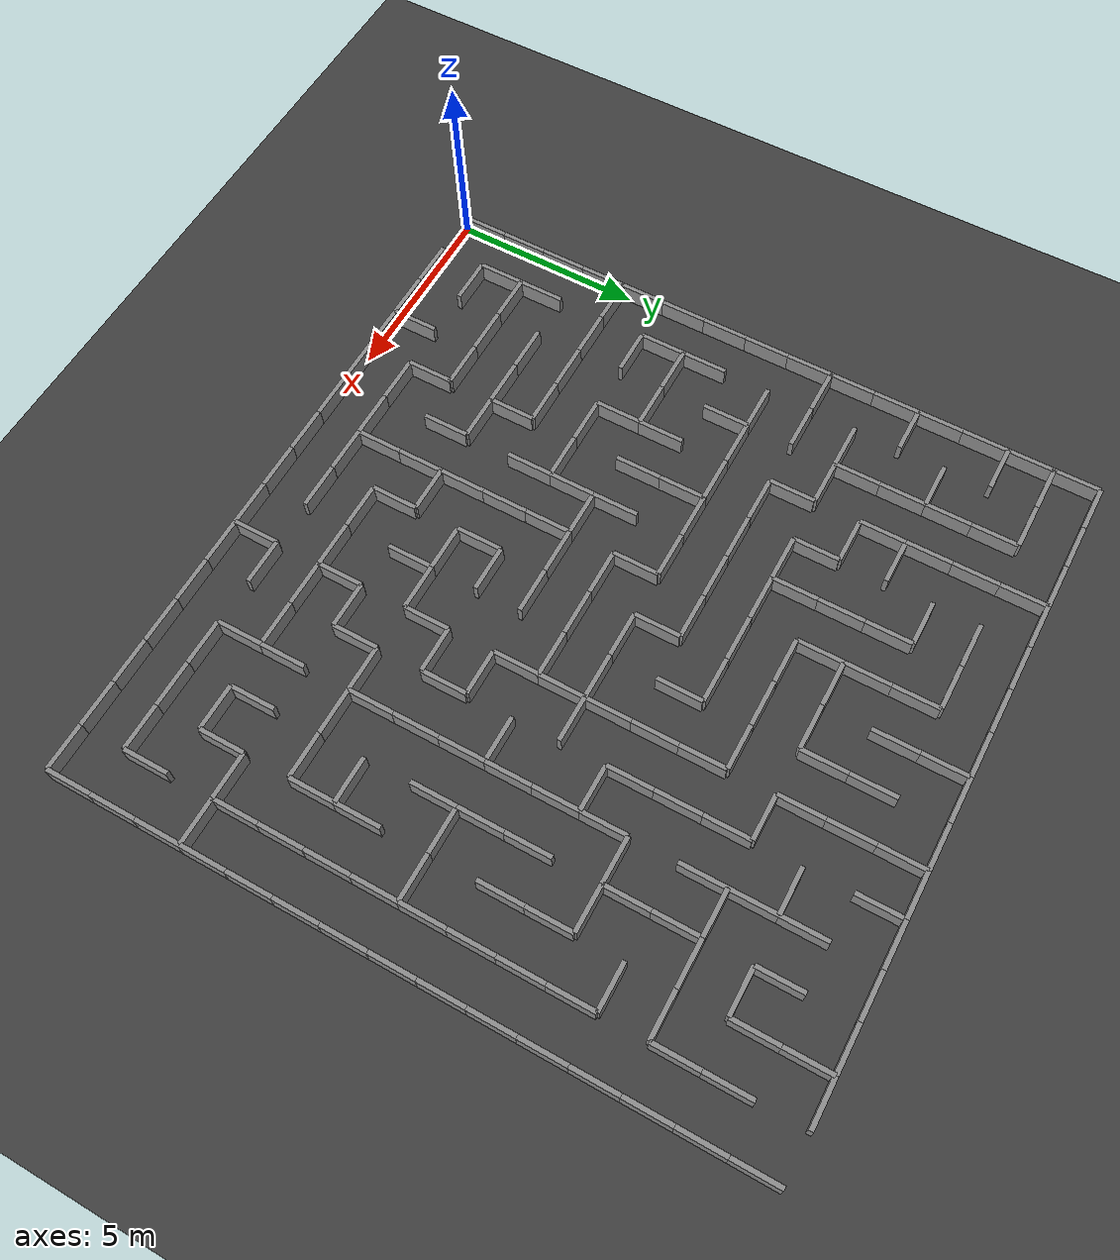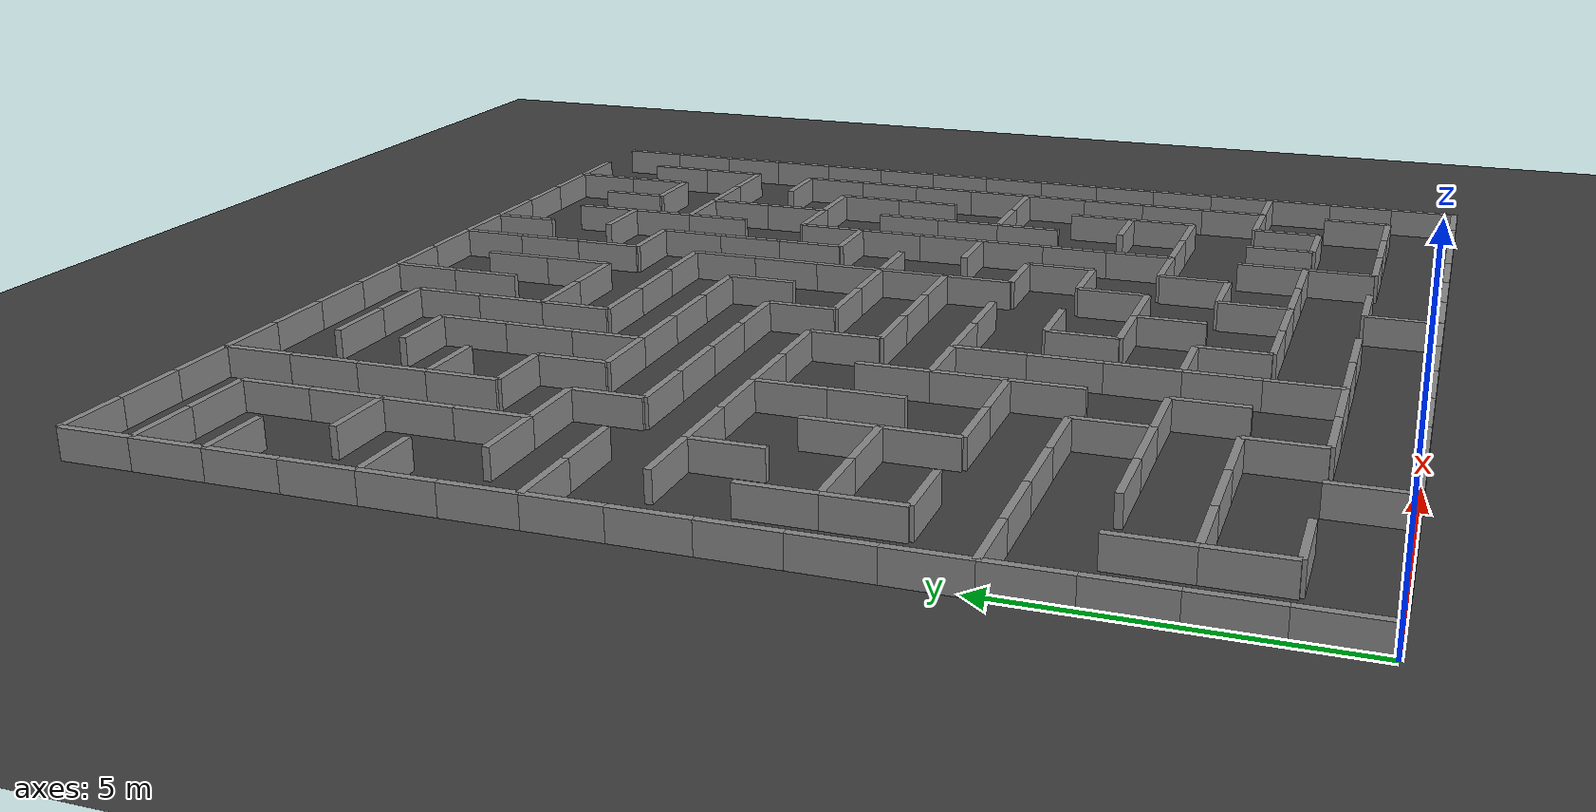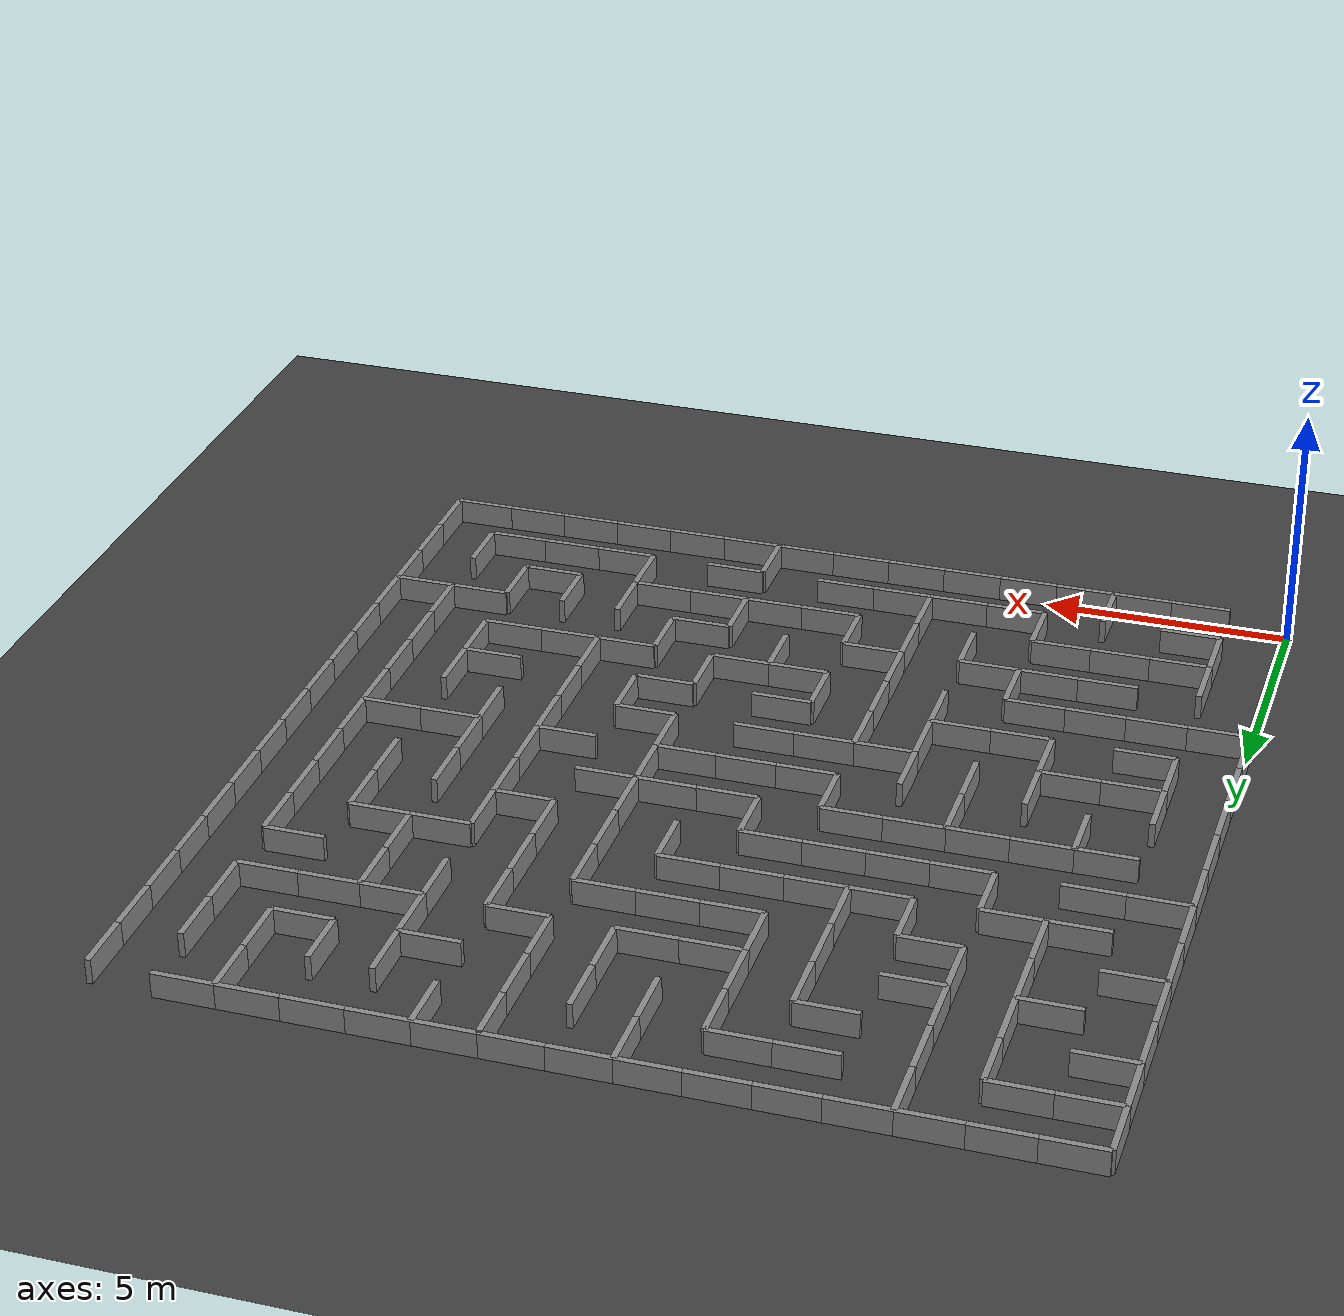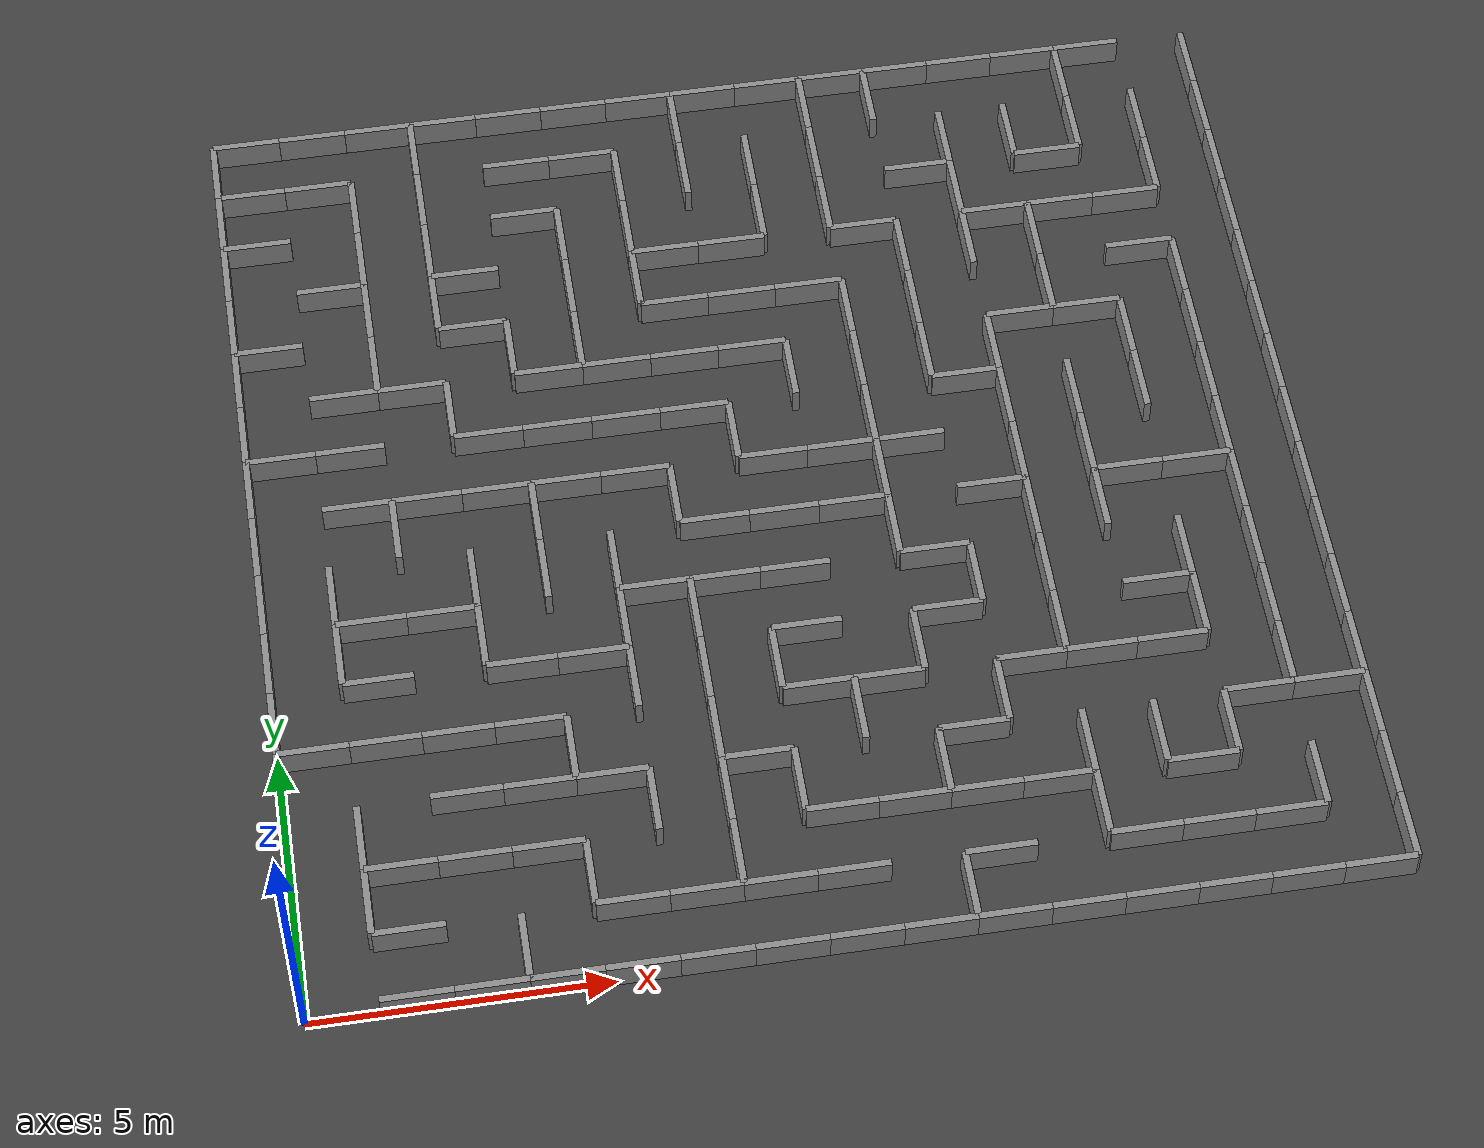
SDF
<?xml version="1.0" ?>
<sdf version="1.9">
  <world name="maze_world">

    <!-- ── Physics ─────────────────────────────────────────────────────── -->
    <physics name="1ms" type="ignored">
      <max_step_size>0.001</max_step_size>
      <real_time_factor>1.0</real_time_factor>
      <real_time_update_rate>1000</real_time_update_rate>
    </physics>

    <!-- ── Required Gazebo Harmonic system plugins ──────────────────────── -->
    <plugin filename="gz-sim-physics-system"
            name="gz::sim::systems::Physics"/>
    <plugin filename="gz-sim-scene-broadcaster-system"
            name="gz::sim::systems::SceneBroadcaster"/>
    <plugin filename="gz-sim-user-commands-system"
            name="gz::sim::systems::UserCommands"/>
    <plugin filename="gz-sim-sensors-system"
            name="gz::sim::systems::Sensors">
      <render_engine>ogre2</render_engine>
    </plugin>
    <plugin filename="gz-sim-contact-system"
            name="gz::sim::systems::Contact"/>
    <plugin filename="gz-sim-imu-system"
            name="gz::sim::systems::Imu"/>

    <!-- ── Scene ────────────────────────────────────────────────────────── -->
    <scene>
      <ambient>0.4 0.4 0.4 1</ambient>
      <background>0.15 0.15 0.15 1</background>
      <shadows>true</shadows>
      <grid>false</grid>
    </scene>

    <!-- ── Directional sunlight ─────────────────────────────────────────── -->
    <light type="directional" name="sun">
      <cast_shadows>true</cast_shadows>
      <pose>0 0 20 0 0 0</pose>
      <diffuse>0.9 0.9 0.9 1</diffuse>
      <specular>0.3 0.3 0.3 1</specular>
      <attenuation>
        <range>1000</range>
        <constant>0.9</constant>
        <linear>0.01</linear>
        <quadratic>0.001</quadratic>
      </attenuation>
      <direction>-0.5 0.2 -0.9</direction>
    </light>

    <!-- ── Ground plane ─────────────────────────────────────────────────── -->
    <model name="ground_plane">
      <static>true</static>
      <link name="link">
        <collision name="col">
          <geometry>
            <plane><normal>0 0 1</normal><size>500 500</size></plane>
          </geometry>
          <surface>
            <friction><ode><mu>1.0</mu><mu2>1.0</mu2></ode></friction>
          </surface>
        </collision>
        <visual name="vis">
          <geometry>
            <plane><normal>0 0 1</normal><size>500 500</size></plane>
          </geometry>
          <material>
            <ambient>0.25 0.25 0.25 1</ambient>
            <diffuse>0.25 0.25 0.25 1</diffuse>
          </material>
        </visual>
      </link>
    </model>

    <!-- ── Maze walls (254 segments) ──────────────────────────────────── -->
    <model name="maze_walls">
      <static>true</static>
      <pose>0 0 0 0 0 0</pose>
      <link name="w0000">
        <pose>0.60000 16.80000 0.25000 0 0 0</pose>
        <collision name="col">
          <geometry><box><size>1.20000 0.12000 0.50000</size></box></geometry>
          <surface>
            <friction><ode><mu>1.0</mu><mu2>1.0</mu2></ode></friction>
            <contact><ode/></contact>
          </surface>
        </collision>
        <visual name="vis">
          <geometry><box><size>1.20000 0.12000 0.50000</size></box></geometry>
          <material>
            <ambient>0.55 0.55 0.55 1</ambient>
            <diffuse>0.55 0.55 0.55 1</diffuse>
            <specular>0.1 0.1 0.1 1</specular>
          </material>
        </visual>
      </link>
      <link name="w0001">
        <pose>1.80000 16.80000 0.25000 0 0 0</pose>
        <collision name="col">
          <geometry><box><size>1.20000 0.12000 0.50000</size></box></geometry>
          <surface>
            <friction><ode><mu>1.0</mu><mu2>1.0</mu2></ode></friction>
            <contact><ode/></contact>
          </surface>
        </collision>
        <visual name="vis">
          <geometry><box><size>1.20000 0.12000 0.50000</size></box></geometry>
          <material>
            <ambient>0.55 0.55 0.55 1</ambient>
            <diffuse>0.55 0.55 0.55 1</diffuse>
            <specular>0.1 0.1 0.1 1</specular>
          </material>
        </visual>
      </link>
      <link name="w0002">
        <pose>3.60000 17.40000 0.25000 0 0 0</pose>
        <collision name="col">
          <geometry><box><size>0.12000 1.20000 0.50000</size></box></geometry>
          <surface>
            <friction><ode><mu>1.0</mu><mu2>1.0</mu2></ode></friction>
            <contact><ode/></contact>
          </surface>
        </collision>
        <visual name="vis">
          <geometry><box><size>0.12000 1.20000 0.50000</size></box></geometry>
          <material>
            <ambient>0.55 0.55 0.55 1</ambient>
            <diffuse>0.55 0.55 0.55 1</diffuse>
            <specular>0.1 0.1 0.1 1</specular>
          </material>
        </visual>
      </link>
      <link name="w0003">
        <pose>5.40000 16.80000 0.25000 0 0 0</pose>
        <collision name="col">
          <geometry><box><size>1.20000 0.12000 0.50000</size></box></geometry>
          <surface>
            <friction><ode><mu>1.0</mu><mu2>1.0</mu2></ode></friction>
            <contact><ode/></contact>
          </surface>
        </collision>
        <visual name="vis">
          <geometry><box><size>1.20000 0.12000 0.50000</size></box></geometry>
          <material>
            <ambient>0.55 0.55 0.55 1</ambient>
            <diffuse>0.55 0.55 0.55 1</diffuse>
            <specular>0.1 0.1 0.1 1</specular>
          </material>
        </visual>
      </link>
      <link name="w0004">
        <pose>6.60000 16.80000 0.25000 0 0 0</pose>
        <collision name="col">
          <geometry><box><size>1.20000 0.12000 0.50000</size></box></geometry>
          <surface>
            <friction><ode><mu>1.0</mu><mu2>1.0</mu2></ode></friction>
            <contact><ode/></contact>
          </surface>
        </collision>
        <visual name="vis">
          <geometry><box><size>1.20000 0.12000 0.50000</size></box></geometry>
          <material>
            <ambient>0.55 0.55 0.55 1</ambient>
            <diffuse>0.55 0.55 0.55 1</diffuse>
            <specular>0.1 0.1 0.1 1</specular>
          </material>
        </visual>
      </link>
      <link name="w0005">
        <pose>8.40000 17.40000 0.25000 0 0 0</pose>
        <collision name="col">
          <geometry><box><size>0.12000 1.20000 0.50000</size></box></geometry>
          <surface>
            <friction><ode><mu>1.0</mu><mu2>1.0</mu2></ode></friction>
            <contact><ode/></contact>
          </surface>
        </collision>
        <visual name="vis">
          <geometry><box><size>0.12000 1.20000 0.50000</size></box></geometry>
          <material>
            <ambient>0.55 0.55 0.55 1</ambient>
            <diffuse>0.55 0.55 0.55 1</diffuse>
            <specular>0.1 0.1 0.1 1</specular>
          </material>
        </visual>
      </link>
      <link name="w0006">
        <pose>10.80000 17.40000 0.25000 0 0 0</pose>
        <collision name="col">
          <geometry><box><size>0.12000 1.20000 0.50000</size></box></geometry>
          <surface>
            <friction><ode><mu>1.0</mu><mu2>1.0</mu2></ode></friction>
            <contact><ode/></contact>
          </surface>
        </collision>
        <visual name="vis">
          <geometry><box><size>0.12000 1.20000 0.50000</size></box></geometry>
          <material>
            <ambient>0.55 0.55 0.55 1</ambient>
            <diffuse>0.55 0.55 0.55 1</diffuse>
            <specular>0.1 0.1 0.1 1</specular>
          </material>
        </visual>
      </link>
      <link name="w0007">
        <pose>12.00000 17.40000 0.25000 0 0 0</pose>
        <collision name="col">
          <geometry><box><size>0.12000 1.20000 0.50000</size></box></geometry>
          <surface>
            <friction><ode><mu>1.0</mu><mu2>1.0</mu2></ode></friction>
            <contact><ode/></contact>
          </surface>
        </collision>
        <visual name="vis">
          <geometry><box><size>0.12000 1.20000 0.50000</size></box></geometry>
          <material>
            <ambient>0.55 0.55 0.55 1</ambient>
            <diffuse>0.55 0.55 0.55 1</diffuse>
            <specular>0.1 0.1 0.1 1</specular>
          </material>
        </visual>
      </link>
      <link name="w0008">
        <pose>15.60000 17.40000 0.25000 0 0 0</pose>
        <collision name="col">
          <geometry><box><size>0.12000 1.20000 0.50000</size></box></geometry>
          <surface>
            <friction><ode><mu>1.0</mu><mu2>1.0</mu2></ode></friction>
            <contact><ode/></contact>
          </surface>
        </collision>
        <visual name="vis">
          <geometry><box><size>0.12000 1.20000 0.50000</size></box></geometry>
          <material>
            <ambient>0.55 0.55 0.55 1</ambient>
            <diffuse>0.55 0.55 0.55 1</diffuse>
            <specular>0.1 0.1 0.1 1</specular>
          </material>
        </visual>
      </link>
      <link name="w0009">
        <pose>18.00000 17.40000 0.25000 0 0 0</pose>
        <collision name="col">
          <geometry><box><size>0.12000 1.20000 0.50000</size></box></geometry>
          <surface>
            <friction><ode><mu>1.0</mu><mu2>1.0</mu2></ode></friction>
            <contact><ode/></contact>
          </surface>
        </collision>
        <visual name="vis">
          <geometry><box><size>0.12000 1.20000 0.50000</size></box></geometry>
          <material>
            <ambient>0.55 0.55 0.55 1</ambient>
            <diffuse>0.55 0.55 0.55 1</diffuse>
            <specular>0.1 0.1 0.1 1</specular>
          </material>
        </visual>
      </link>
      <link name="w0010">
        <pose>0.60000 15.60000 0.25000 0 0 0</pose>
        <collision name="col">
          <geometry><box><size>1.20000 0.12000 0.50000</size></box></geometry>
          <surface>
            <friction><ode><mu>1.0</mu><mu2>1.0</mu2></ode></friction>
            <contact><ode/></contact>
          </surface>
        </collision>
        <visual name="vis">
          <geometry><box><size>1.20000 0.12000 0.50000</size></box></geometry>
          <material>
            <ambient>0.55 0.55 0.55 1</ambient>
            <diffuse>0.55 0.55 0.55 1</diffuse>
            <specular>0.1 0.1 0.1 1</specular>
          </material>
        </visual>
      </link>
      <link name="w0011">
        <pose>2.40000 16.20000 0.25000 0 0 0</pose>
        <collision name="col">
          <geometry><box><size>0.12000 1.20000 0.50000</size></box></geometry>
          <surface>
            <friction><ode><mu>1.0</mu><mu2>1.0</mu2></ode></friction>
            <contact><ode/></contact>
          </surface>
        </collision>
        <visual name="vis">
          <geometry><box><size>0.12000 1.20000 0.50000</size></box></geometry>
          <material>
            <ambient>0.55 0.55 0.55 1</ambient>
            <diffuse>0.55 0.55 0.55 1</diffuse>
            <specular>0.1 0.1 0.1 1</specular>
          </material>
        </visual>
      </link>
      <link name="w0012">
        <pose>3.60000 16.20000 0.25000 0 0 0</pose>
        <collision name="col">
          <geometry><box><size>0.12000 1.20000 0.50000</size></box></geometry>
          <surface>
            <friction><ode><mu>1.0</mu><mu2>1.0</mu2></ode></friction>
            <contact><ode/></contact>
          </surface>
        </collision>
        <visual name="vis">
          <geometry><box><size>0.12000 1.20000 0.50000</size></box></geometry>
          <material>
            <ambient>0.55 0.55 0.55 1</ambient>
            <diffuse>0.55 0.55 0.55 1</diffuse>
            <specular>0.1 0.1 0.1 1</specular>
          </material>
        </visual>
      </link>
      <link name="w0013">
        <pose>5.40000 15.60000 0.25000 0 0 0</pose>
        <collision name="col">
          <geometry><box><size>1.20000 0.12000 0.50000</size></box></geometry>
          <surface>
            <friction><ode><mu>1.0</mu><mu2>1.0</mu2></ode></friction>
            <contact><ode/></contact>
          </surface>
        </collision>
        <visual name="vis">
          <geometry><box><size>1.20000 0.12000 0.50000</size></box></geometry>
          <material>
            <ambient>0.55 0.55 0.55 1</ambient>
            <diffuse>0.55 0.55 0.55 1</diffuse>
            <specular>0.1 0.1 0.1 1</specular>
          </material>
        </visual>
      </link>
      <link name="w0014">
        <pose>7.20000 16.20000 0.25000 0 0 0</pose>
        <collision name="col">
          <geometry><box><size>0.12000 1.20000 0.50000</size></box></geometry>
          <surface>
            <friction><ode><mu>1.0</mu><mu2>1.0</mu2></ode></friction>
            <contact><ode/></contact>
          </surface>
        </collision>
        <visual name="vis">
          <geometry><box><size>0.12000 1.20000 0.50000</size></box></geometry>
          <material>
            <ambient>0.55 0.55 0.55 1</ambient>
            <diffuse>0.55 0.55 0.55 1</diffuse>
            <specular>0.1 0.1 0.1 1</specular>
          </material>
        </visual>
      </link>
      <link name="w0015">
        <pose>8.40000 16.20000 0.25000 0 0 0</pose>
        <collision name="col">
          <geometry><box><size>0.12000 1.20000 0.50000</size></box></geometry>
          <surface>
            <friction><ode><mu>1.0</mu><mu2>1.0</mu2></ode></friction>
            <contact><ode/></contact>
          </surface>
        </collision>
        <visual name="vis">
          <geometry><box><size>0.12000 1.20000 0.50000</size></box></geometry>
          <material>
            <ambient>0.55 0.55 0.55 1</ambient>
            <diffuse>0.55 0.55 0.55 1</diffuse>
            <specular>0.1 0.1 0.1 1</specular>
          </material>
        </visual>
      </link>
      <link name="w0016">
        <pose>9.60000 16.20000 0.25000 0 0 0</pose>
        <collision name="col">
          <geometry><box><size>0.12000 1.20000 0.50000</size></box></geometry>
          <surface>
            <friction><ode><mu>1.0</mu><mu2>1.0</mu2></ode></friction>
            <contact><ode/></contact>
          </surface>
        </collision>
        <visual name="vis">
          <geometry><box><size>0.12000 1.20000 0.50000</size></box></geometry>
          <material>
            <ambient>0.55 0.55 0.55 1</ambient>
            <diffuse>0.55 0.55 0.55 1</diffuse>
            <specular>0.1 0.1 0.1 1</specular>
          </material>
        </visual>
      </link>
      <link name="w0017">
        <pose>10.80000 16.20000 0.25000 0 0 0</pose>
        <collision name="col">
          <geometry><box><size>0.12000 1.20000 0.50000</size></box></geometry>
          <surface>
            <friction><ode><mu>1.0</mu><mu2>1.0</mu2></ode></friction>
            <contact><ode/></contact>
          </surface>
        </collision>
        <visual name="vis">
          <geometry><box><size>0.12000 1.20000 0.50000</size></box></geometry>
          <material>
            <ambient>0.55 0.55 0.55 1</ambient>
            <diffuse>0.55 0.55 0.55 1</diffuse>
            <specular>0.1 0.1 0.1 1</specular>
          </material>
        </visual>
      </link>
      <link name="w0018">
        <pose>12.60000 15.60000 0.25000 0 0 0</pose>
        <collision name="col">
          <geometry><box><size>1.20000 0.12000 0.50000</size></box></geometry>
          <surface>
            <friction><ode><mu>1.0</mu><mu2>1.0</mu2></ode></friction>
            <contact><ode/></contact>
          </surface>
        </collision>
        <visual name="vis">
          <geometry><box><size>1.20000 0.12000 0.50000</size></box></geometry>
          <material>
            <ambient>0.55 0.55 0.55 1</ambient>
            <diffuse>0.55 0.55 0.55 1</diffuse>
            <specular>0.1 0.1 0.1 1</specular>
          </material>
        </visual>
      </link>
      <link name="w0019">
        <pose>13.20000 16.20000 0.25000 0 0 0</pose>
        <collision name="col">
          <geometry><box><size>0.12000 1.20000 0.50000</size></box></geometry>
          <surface>
            <friction><ode><mu>1.0</mu><mu2>1.0</mu2></ode></friction>
            <contact><ode/></contact>
          </surface>
        </collision>
        <visual name="vis">
          <geometry><box><size>0.12000 1.20000 0.50000</size></box></geometry>
          <material>
            <ambient>0.55 0.55 0.55 1</ambient>
            <diffuse>0.55 0.55 0.55 1</diffuse>
            <specular>0.1 0.1 0.1 1</specular>
          </material>
        </visual>
      </link>
      <link name="w0020">
        <pose>14.40000 16.20000 0.25000 0 0 0</pose>
        <collision name="col">
          <geometry><box><size>0.12000 1.20000 0.50000</size></box></geometry>
          <surface>
            <friction><ode><mu>1.0</mu><mu2>1.0</mu2></ode></friction>
            <contact><ode/></contact>
          </surface>
        </collision>
        <visual name="vis">
          <geometry><box><size>0.12000 1.20000 0.50000</size></box></geometry>
          <material>
            <ambient>0.55 0.55 0.55 1</ambient>
            <diffuse>0.55 0.55 0.55 1</diffuse>
            <specular>0.1 0.1 0.1 1</specular>
          </material>
        </visual>
      </link>
      <link name="w0021">
        <pose>15.00000 15.60000 0.25000 0 0 0</pose>
        <collision name="col">
          <geometry><box><size>1.20000 0.12000 0.50000</size></box></geometry>
          <surface>
            <friction><ode><mu>1.0</mu><mu2>1.0</mu2></ode></friction>
            <contact><ode/></contact>
          </surface>
        </collision>
        <visual name="vis">
          <geometry><box><size>1.20000 0.12000 0.50000</size></box></geometry>
          <material>
            <ambient>0.55 0.55 0.55 1</ambient>
            <diffuse>0.55 0.55 0.55 1</diffuse>
            <specular>0.1 0.1 0.1 1</specular>
          </material>
        </visual>
      </link>
      <link name="w0022">
        <pose>15.60000 16.20000 0.25000 0 0 0</pose>
        <collision name="col">
          <geometry><box><size>0.12000 1.20000 0.50000</size></box></geometry>
          <surface>
            <friction><ode><mu>1.0</mu><mu2>1.0</mu2></ode></friction>
            <contact><ode/></contact>
          </surface>
        </collision>
        <visual name="vis">
          <geometry><box><size>0.12000 1.20000 0.50000</size></box></geometry>
          <material>
            <ambient>0.55 0.55 0.55 1</ambient>
            <diffuse>0.55 0.55 0.55 1</diffuse>
            <specular>0.1 0.1 0.1 1</specular>
          </material>
        </visual>
      </link>
      <link name="w0023">
        <pose>16.80000 16.20000 0.25000 0 0 0</pose>
        <collision name="col">
          <geometry><box><size>0.12000 1.20000 0.50000</size></box></geometry>
          <surface>
            <friction><ode><mu>1.0</mu><mu2>1.0</mu2></ode></friction>
            <contact><ode/></contact>
          </surface>
        </collision>
        <visual name="vis">
          <geometry><box><size>0.12000 1.20000 0.50000</size></box></geometry>
          <material>
            <ambient>0.55 0.55 0.55 1</ambient>
            <diffuse>0.55 0.55 0.55 1</diffuse>
            <specular>0.1 0.1 0.1 1</specular>
          </material>
        </visual>
      </link>
      <link name="w0024">
        <pose>18.00000 16.20000 0.25000 0 0 0</pose>
        <collision name="col">
          <geometry><box><size>0.12000 1.20000 0.50000</size></box></geometry>
          <surface>
            <friction><ode><mu>1.0</mu><mu2>1.0</mu2></ode></friction>
            <contact><ode/></contact>
          </surface>
        </collision>
        <visual name="vis">
          <geometry><box><size>0.12000 1.20000 0.50000</size></box></geometry>
          <material>
            <ambient>0.55 0.55 0.55 1</ambient>
            <diffuse>0.55 0.55 0.55 1</diffuse>
            <specular>0.1 0.1 0.1 1</specular>
          </material>
        </visual>
      </link>
      <link name="w0025">
        <pose>1.80000 14.40000 0.25000 0 0 0</pose>
        <collision name="col">
          <geometry><box><size>1.20000 0.12000 0.50000</size></box></geometry>
          <surface>
            <friction><ode><mu>1.0</mu><mu2>1.0</mu2></ode></friction>
            <contact><ode/></contact>
          </surface>
        </collision>
        <visual name="vis">
          <geometry><box><size>1.20000 0.12000 0.50000</size></box></geometry>
          <material>
            <ambient>0.55 0.55 0.55 1</ambient>
            <diffuse>0.55 0.55 0.55 1</diffuse>
            <specular>0.1 0.1 0.1 1</specular>
          </material>
        </visual>
      </link>
      <link name="w0026">
        <pose>2.40000 15.00000 0.25000 0 0 0</pose>
        <collision name="col">
          <geometry><box><size>0.12000 1.20000 0.50000</size></box></geometry>
          <surface>
            <friction><ode><mu>1.0</mu><mu2>1.0</mu2></ode></friction>
            <contact><ode/></contact>
          </surface>
        </collision>
        <visual name="vis">
          <geometry><box><size>0.12000 1.20000 0.50000</size></box></geometry>
          <material>
            <ambient>0.55 0.55 0.55 1</ambient>
            <diffuse>0.55 0.55 0.55 1</diffuse>
            <specular>0.1 0.1 0.1 1</specular>
          </material>
        </visual>
      </link>
      <link name="w0027">
        <pose>3.60000 15.00000 0.25000 0 0 0</pose>
        <collision name="col">
          <geometry><box><size>0.12000 1.20000 0.50000</size></box></geometry>
          <surface>
            <friction><ode><mu>1.0</mu><mu2>1.0</mu2></ode></friction>
            <contact><ode/></contact>
          </surface>
        </collision>
        <visual name="vis">
          <geometry><box><size>0.12000 1.20000 0.50000</size></box></geometry>
          <material>
            <ambient>0.55 0.55 0.55 1</ambient>
            <diffuse>0.55 0.55 0.55 1</diffuse>
            <specular>0.1 0.1 0.1 1</specular>
          </material>
        </visual>
      </link>
      <link name="w0028">
        <pose>4.20000 14.40000 0.25000 0 0 0</pose>
        <collision name="col">
          <geometry><box><size>1.20000 0.12000 0.50000</size></box></geometry>
          <surface>
            <friction><ode><mu>1.0</mu><mu2>1.0</mu2></ode></friction>
            <contact><ode/></contact>
          </surface>
        </collision>
        <visual name="vis">
          <geometry><box><size>1.20000 0.12000 0.50000</size></box></geometry>
          <material>
            <ambient>0.55 0.55 0.55 1</ambient>
            <diffuse>0.55 0.55 0.55 1</diffuse>
            <specular>0.1 0.1 0.1 1</specular>
          </material>
        </visual>
      </link>
      <link name="w0029">
        <pose>6.00000 15.00000 0.25000 0 0 0</pose>
        <collision name="col">
          <geometry><box><size>0.12000 1.20000 0.50000</size></box></geometry>
          <surface>
            <friction><ode><mu>1.0</mu><mu2>1.0</mu2></ode></friction>
            <contact><ode/></contact>
          </surface>
        </collision>
        <visual name="vis">
          <geometry><box><size>0.12000 1.20000 0.50000</size></box></geometry>
          <material>
            <ambient>0.55 0.55 0.55 1</ambient>
            <diffuse>0.55 0.55 0.55 1</diffuse>
            <specular>0.1 0.1 0.1 1</specular>
          </material>
        </visual>
      </link>
      <link name="w0030">
        <pose>7.20000 15.00000 0.25000 0 0 0</pose>
        <collision name="col">
          <geometry><box><size>0.12000 1.20000 0.50000</size></box></geometry>
          <surface>
            <friction><ode><mu>1.0</mu><mu2>1.0</mu2></ode></friction>
            <contact><ode/></contact>
          </surface>
        </collision>
        <visual name="vis">
          <geometry><box><size>0.12000 1.20000 0.50000</size></box></geometry>
          <material>
            <ambient>0.55 0.55 0.55 1</ambient>
            <diffuse>0.55 0.55 0.55 1</diffuse>
            <specular>0.1 0.1 0.1 1</specular>
          </material>
        </visual>
      </link>
      <link name="w0031">
        <pose>7.80000 14.40000 0.25000 0 0 0</pose>
        <collision name="col">
          <geometry><box><size>1.20000 0.12000 0.50000</size></box></geometry>
          <surface>
            <friction><ode><mu>1.0</mu><mu2>1.0</mu2></ode></friction>
            <contact><ode/></contact>
          </surface>
        </collision>
        <visual name="vis">
          <geometry><box><size>1.20000 0.12000 0.50000</size></box></geometry>
          <material>
            <ambient>0.55 0.55 0.55 1</ambient>
            <diffuse>0.55 0.55 0.55 1</diffuse>
            <specular>0.1 0.1 0.1 1</specular>
          </material>
        </visual>
      </link>
      <link name="w0032">
        <pose>9.00000 14.40000 0.25000 0 0 0</pose>
        <collision name="col">
          <geometry><box><size>1.20000 0.12000 0.50000</size></box></geometry>
          <surface>
            <friction><ode><mu>1.0</mu><mu2>1.0</mu2></ode></friction>
            <contact><ode/></contact>
          </surface>
        </collision>
        <visual name="vis">
          <geometry><box><size>1.20000 0.12000 0.50000</size></box></geometry>
          <material>
            <ambient>0.55 0.55 0.55 1</ambient>
            <diffuse>0.55 0.55 0.55 1</diffuse>
            <specular>0.1 0.1 0.1 1</specular>
          </material>
        </visual>
      </link>
      <link name="w0033">
        <pose>9.60000 15.00000 0.25000 0 0 0</pose>
        <collision name="col">
          <geometry><box><size>0.12000 1.20000 0.50000</size></box></geometry>
          <surface>
            <friction><ode><mu>1.0</mu><mu2>1.0</mu2></ode></friction>
            <contact><ode/></contact>
          </surface>
        </collision>
        <visual name="vis">
          <geometry><box><size>0.12000 1.20000 0.50000</size></box></geometry>
          <material>
            <ambient>0.55 0.55 0.55 1</ambient>
            <diffuse>0.55 0.55 0.55 1</diffuse>
            <specular>0.1 0.1 0.1 1</specular>
          </material>
        </visual>
      </link>
      <link name="w0034">
        <pose>10.80000 15.00000 0.25000 0 0 0</pose>
        <collision name="col">
          <geometry><box><size>0.12000 1.20000 0.50000</size></box></geometry>
          <surface>
            <friction><ode><mu>1.0</mu><mu2>1.0</mu2></ode></friction>
            <contact><ode/></contact>
          </surface>
        </collision>
        <visual name="vis">
          <geometry><box><size>0.12000 1.20000 0.50000</size></box></geometry>
          <material>
            <ambient>0.55 0.55 0.55 1</ambient>
            <diffuse>0.55 0.55 0.55 1</diffuse>
            <specular>0.1 0.1 0.1 1</specular>
          </material>
        </visual>
      </link>
      <link name="w0035">
        <pose>11.40000 14.40000 0.25000 0 0 0</pose>
        <collision name="col">
          <geometry><box><size>1.20000 0.12000 0.50000</size></box></geometry>
          <surface>
            <friction><ode><mu>1.0</mu><mu2>1.0</mu2></ode></friction>
            <contact><ode/></contact>
          </surface>
        </collision>
        <visual name="vis">
          <geometry><box><size>1.20000 0.12000 0.50000</size></box></geometry>
          <material>
            <ambient>0.55 0.55 0.55 1</ambient>
            <diffuse>0.55 0.55 0.55 1</diffuse>
            <specular>0.1 0.1 0.1 1</specular>
          </material>
        </visual>
      </link>
      <link name="w0036">
        <pose>13.20000 15.00000 0.25000 0 0 0</pose>
        <collision name="col">
          <geometry><box><size>0.12000 1.20000 0.50000</size></box></geometry>
          <surface>
            <friction><ode><mu>1.0</mu><mu2>1.0</mu2></ode></friction>
            <contact><ode/></contact>
          </surface>
        </collision>
        <visual name="vis">
          <geometry><box><size>0.12000 1.20000 0.50000</size></box></geometry>
          <material>
            <ambient>0.55 0.55 0.55 1</ambient>
            <diffuse>0.55 0.55 0.55 1</diffuse>
            <specular>0.1 0.1 0.1 1</specular>
          </material>
        </visual>
      </link>
      <link name="w0037">
        <pose>13.80000 14.40000 0.25000 0 0 0</pose>
        <collision name="col">
          <geometry><box><size>1.20000 0.12000 0.50000</size></box></geometry>
          <surface>
            <friction><ode><mu>1.0</mu><mu2>1.0</mu2></ode></friction>
            <contact><ode/></contact>
          </surface>
        </collision>
        <visual name="vis">
          <geometry><box><size>1.20000 0.12000 0.50000</size></box></geometry>
          <material>
            <ambient>0.55 0.55 0.55 1</ambient>
            <diffuse>0.55 0.55 0.55 1</diffuse>
            <specular>0.1 0.1 0.1 1</specular>
          </material>
        </visual>
      </link>
      <link name="w0038">
        <pose>15.00000 14.40000 0.25000 0 0 0</pose>
        <collision name="col">
          <geometry><box><size>1.20000 0.12000 0.50000</size></box></geometry>
          <surface>
            <friction><ode><mu>1.0</mu><mu2>1.0</mu2></ode></friction>
            <contact><ode/></contact>
          </surface>
        </collision>
        <visual name="vis">
          <geometry><box><size>1.20000 0.12000 0.50000</size></box></geometry>
          <material>
            <ambient>0.55 0.55 0.55 1</ambient>
            <diffuse>0.55 0.55 0.55 1</diffuse>
            <specular>0.1 0.1 0.1 1</specular>
          </material>
        </visual>
      </link>
      <link name="w0039">
        <pose>16.20000 14.40000 0.25000 0 0 0</pose>
        <collision name="col">
          <geometry><box><size>1.20000 0.12000 0.50000</size></box></geometry>
          <surface>
            <friction><ode><mu>1.0</mu><mu2>1.0</mu2></ode></friction>
            <contact><ode/></contact>
          </surface>
        </collision>
        <visual name="vis">
          <geometry><box><size>1.20000 0.12000 0.50000</size></box></geometry>
          <material>
            <ambient>0.55 0.55 0.55 1</ambient>
            <diffuse>0.55 0.55 0.55 1</diffuse>
            <specular>0.1 0.1 0.1 1</specular>
          </material>
        </visual>
      </link>
      <link name="w0040">
        <pose>16.80000 15.00000 0.25000 0 0 0</pose>
        <collision name="col">
          <geometry><box><size>0.12000 1.20000 0.50000</size></box></geometry>
          <surface>
            <friction><ode><mu>1.0</mu><mu2>1.0</mu2></ode></friction>
            <contact><ode/></contact>
          </surface>
        </collision>
        <visual name="vis">
          <geometry><box><size>0.12000 1.20000 0.50000</size></box></geometry>
          <material>
            <ambient>0.55 0.55 0.55 1</ambient>
            <diffuse>0.55 0.55 0.55 1</diffuse>
            <specular>0.1 0.1 0.1 1</specular>
          </material>
        </visual>
      </link>
      <link name="w0041">
        <pose>18.00000 15.00000 0.25000 0 0 0</pose>
        <collision name="col">
          <geometry><box><size>0.12000 1.20000 0.50000</size></box></geometry>
          <surface>
            <friction><ode><mu>1.0</mu><mu2>1.0</mu2></ode></friction>
            <contact><ode/></contact>
          </surface>
        </collision>
        <visual name="vis">
          <geometry><box><size>0.12000 1.20000 0.50000</size></box></geometry>
          <material>
            <ambient>0.55 0.55 0.55 1</ambient>
            <diffuse>0.55 0.55 0.55 1</diffuse>
            <specular>0.1 0.1 0.1 1</specular>
          </material>
        </visual>
      </link>
      <link name="w0042">
        <pose>0.60000 13.20000 0.25000 0 0 0</pose>
        <collision name="col">
          <geometry><box><size>1.20000 0.12000 0.50000</size></box></geometry>
          <surface>
            <friction><ode><mu>1.0</mu><mu2>1.0</mu2></ode></friction>
            <contact><ode/></contact>
          </surface>
        </collision>
        <visual name="vis">
          <geometry><box><size>1.20000 0.12000 0.50000</size></box></geometry>
          <material>
            <ambient>0.55 0.55 0.55 1</ambient>
            <diffuse>0.55 0.55 0.55 1</diffuse>
            <specular>0.1 0.1 0.1 1</specular>
          </material>
        </visual>
      </link>
      <link name="w0043">
        <pose>2.40000 13.80000 0.25000 0 0 0</pose>
        <collision name="col">
          <geometry><box><size>0.12000 1.20000 0.50000</size></box></geometry>
          <surface>
            <friction><ode><mu>1.0</mu><mu2>1.0</mu2></ode></friction>
            <contact><ode/></contact>
          </surface>
        </collision>
        <visual name="vis">
          <geometry><box><size>0.12000 1.20000 0.50000</size></box></geometry>
          <material>
            <ambient>0.55 0.55 0.55 1</ambient>
            <diffuse>0.55 0.55 0.55 1</diffuse>
            <specular>0.1 0.1 0.1 1</specular>
          </material>
        </visual>
      </link>
      <link name="w0044">
        <pose>3.60000 13.80000 0.25000 0 0 0</pose>
        <collision name="col">
          <geometry><box><size>0.12000 1.20000 0.50000</size></box></geometry>
          <surface>
            <friction><ode><mu>1.0</mu><mu2>1.0</mu2></ode></friction>
            <contact><ode/></contact>
          </surface>
        </collision>
        <visual name="vis">
          <geometry><box><size>0.12000 1.20000 0.50000</size></box></geometry>
          <material>
            <ambient>0.55 0.55 0.55 1</ambient>
            <diffuse>0.55 0.55 0.55 1</diffuse>
            <specular>0.1 0.1 0.1 1</specular>
          </material>
        </visual>
      </link>
      <link name="w0045">
        <pose>4.20000 13.20000 0.25000 0 0 0</pose>
        <collision name="col">
          <geometry><box><size>1.20000 0.12000 0.50000</size></box></geometry>
          <surface>
            <friction><ode><mu>1.0</mu><mu2>1.0</mu2></ode></friction>
            <contact><ode/></contact>
          </surface>
        </collision>
        <visual name="vis">
          <geometry><box><size>1.20000 0.12000 0.50000</size></box></geometry>
          <material>
            <ambient>0.55 0.55 0.55 1</ambient>
            <diffuse>0.55 0.55 0.55 1</diffuse>
            <specular>0.1 0.1 0.1 1</specular>
          </material>
        </visual>
      </link>
      <link name="w0046">
        <pose>6.00000 13.80000 0.25000 0 0 0</pose>
        <collision name="col">
          <geometry><box><size>0.12000 1.20000 0.50000</size></box></geometry>
          <surface>
            <friction><ode><mu>1.0</mu><mu2>1.0</mu2></ode></friction>
            <contact><ode/></contact>
          </surface>
        </collision>
        <visual name="vis">
          <geometry><box><size>0.12000 1.20000 0.50000</size></box></geometry>
          <material>
            <ambient>0.55 0.55 0.55 1</ambient>
            <diffuse>0.55 0.55 0.55 1</diffuse>
            <specular>0.1 0.1 0.1 1</specular>
          </material>
        </visual>
      </link>
      <link name="w0047">
        <pose>7.20000 13.80000 0.25000 0 0 0</pose>
        <collision name="col">
          <geometry><box><size>0.12000 1.20000 0.50000</size></box></geometry>
          <surface>
            <friction><ode><mu>1.0</mu><mu2>1.0</mu2></ode></friction>
            <contact><ode/></contact>
          </surface>
        </collision>
        <visual name="vis">
          <geometry><box><size>0.12000 1.20000 0.50000</size></box></geometry>
          <material>
            <ambient>0.55 0.55 0.55 1</ambient>
            <diffuse>0.55 0.55 0.55 1</diffuse>
            <specular>0.1 0.1 0.1 1</specular>
          </material>
        </visual>
      </link>
      <link name="w0048">
        <pose>7.80000 13.20000 0.25000 0 0 0</pose>
        <collision name="col">
          <geometry><box><size>1.20000 0.12000 0.50000</size></box></geometry>
          <surface>
            <friction><ode><mu>1.0</mu><mu2>1.0</mu2></ode></friction>
            <contact><ode/></contact>
          </surface>
        </collision>
        <visual name="vis">
          <geometry><box><size>1.20000 0.12000 0.50000</size></box></geometry>
          <material>
            <ambient>0.55 0.55 0.55 1</ambient>
            <diffuse>0.55 0.55 0.55 1</diffuse>
            <specular>0.1 0.1 0.1 1</specular>
          </material>
        </visual>
      </link>
      <link name="w0049">
        <pose>9.00000 13.20000 0.25000 0 0 0</pose>
        <collision name="col">
          <geometry><box><size>1.20000 0.12000 0.50000</size></box></geometry>
          <surface>
            <friction><ode><mu>1.0</mu><mu2>1.0</mu2></ode></friction>
            <contact><ode/></contact>
          </surface>
        </collision>
        <visual name="vis">
          <geometry><box><size>1.20000 0.12000 0.50000</size></box></geometry>
          <material>
            <ambient>0.55 0.55 0.55 1</ambient>
            <diffuse>0.55 0.55 0.55 1</diffuse>
            <specular>0.1 0.1 0.1 1</specular>
          </material>
        </visual>
      </link>
      <link name="w0050">
        <pose>10.20000 13.20000 0.25000 0 0 0</pose>
        <collision name="col">
          <geometry><box><size>1.20000 0.12000 0.50000</size></box></geometry>
          <surface>
            <friction><ode><mu>1.0</mu><mu2>1.0</mu2></ode></friction>
            <contact><ode/></contact>
          </surface>
        </collision>
        <visual name="vis">
          <geometry><box><size>1.20000 0.12000 0.50000</size></box></geometry>
          <material>
            <ambient>0.55 0.55 0.55 1</ambient>
            <diffuse>0.55 0.55 0.55 1</diffuse>
            <specular>0.1 0.1 0.1 1</specular>
          </material>
        </visual>
      </link>
      <link name="w0051">
        <pose>12.00000 13.80000 0.25000 0 0 0</pose>
        <collision name="col">
          <geometry><box><size>0.12000 1.20000 0.50000</size></box></geometry>
          <surface>
            <friction><ode><mu>1.0</mu><mu2>1.0</mu2></ode></friction>
            <contact><ode/></contact>
          </surface>
        </collision>
        <visual name="vis">
          <geometry><box><size>0.12000 1.20000 0.50000</size></box></geometry>
          <material>
            <ambient>0.55 0.55 0.55 1</ambient>
            <diffuse>0.55 0.55 0.55 1</diffuse>
            <specular>0.1 0.1 0.1 1</specular>
          </material>
        </visual>
      </link>
      <link name="w0052">
        <pose>13.20000 13.80000 0.25000 0 0 0</pose>
        <collision name="col">
          <geometry><box><size>0.12000 1.20000 0.50000</size></box></geometry>
          <surface>
            <friction><ode><mu>1.0</mu><mu2>1.0</mu2></ode></friction>
            <contact><ode/></contact>
          </surface>
        </collision>
        <visual name="vis">
          <geometry><box><size>0.12000 1.20000 0.50000</size></box></geometry>
          <material>
            <ambient>0.55 0.55 0.55 1</ambient>
            <diffuse>0.55 0.55 0.55 1</diffuse>
            <specular>0.1 0.1 0.1 1</specular>
          </material>
        </visual>
      </link>
      <link name="w0053">
        <pose>14.40000 13.80000 0.25000 0 0 0</pose>
        <collision name="col">
          <geometry><box><size>0.12000 1.20000 0.50000</size></box></geometry>
          <surface>
            <friction><ode><mu>1.0</mu><mu2>1.0</mu2></ode></friction>
            <contact><ode/></contact>
          </surface>
        </collision>
        <visual name="vis">
          <geometry><box><size>0.12000 1.20000 0.50000</size></box></geometry>
          <material>
            <ambient>0.55 0.55 0.55 1</ambient>
            <diffuse>0.55 0.55 0.55 1</diffuse>
            <specular>0.1 0.1 0.1 1</specular>
          </material>
        </visual>
      </link>
      <link name="w0054">
        <pose>16.20000 13.20000 0.25000 0 0 0</pose>
        <collision name="col">
          <geometry><box><size>1.20000 0.12000 0.50000</size></box></geometry>
          <surface>
            <friction><ode><mu>1.0</mu><mu2>1.0</mu2></ode></friction>
            <contact><ode/></contact>
          </surface>
        </collision>
        <visual name="vis">
          <geometry><box><size>1.20000 0.12000 0.50000</size></box></geometry>
          <material>
            <ambient>0.55 0.55 0.55 1</ambient>
            <diffuse>0.55 0.55 0.55 1</diffuse>
            <specular>0.1 0.1 0.1 1</specular>
          </material>
        </visual>
      </link>
      <link name="w0055">
        <pose>18.00000 13.80000 0.25000 0 0 0</pose>
        <collision name="col">
          <geometry><box><size>0.12000 1.20000 0.50000</size></box></geometry>
          <surface>
            <friction><ode><mu>1.0</mu><mu2>1.0</mu2></ode></friction>
            <contact><ode/></contact>
          </surface>
        </collision>
        <visual name="vis">
          <geometry><box><size>0.12000 1.20000 0.50000</size></box></geometry>
          <material>
            <ambient>0.55 0.55 0.55 1</ambient>
            <diffuse>0.55 0.55 0.55 1</diffuse>
            <specular>0.1 0.1 0.1 1</specular>
          </material>
        </visual>
      </link>
      <link name="w0056">
        <pose>1.80000 12.00000 0.25000 0 0 0</pose>
        <collision name="col">
          <geometry><box><size>1.20000 0.12000 0.50000</size></box></geometry>
          <surface>
            <friction><ode><mu>1.0</mu><mu2>1.0</mu2></ode></friction>
            <contact><ode/></contact>
          </surface>
        </collision>
        <visual name="vis">
          <geometry><box><size>1.20000 0.12000 0.50000</size></box></geometry>
          <material>
            <ambient>0.55 0.55 0.55 1</ambient>
            <diffuse>0.55 0.55 0.55 1</diffuse>
            <specular>0.1 0.1 0.1 1</specular>
          </material>
        </visual>
      </link>
      <link name="w0057">
        <pose>2.40000 12.60000 0.25000 0 0 0</pose>
        <collision name="col">
          <geometry><box><size>0.12000 1.20000 0.50000</size></box></geometry>
          <surface>
            <friction><ode><mu>1.0</mu><mu2>1.0</mu2></ode></friction>
            <contact><ode/></contact>
          </surface>
        </collision>
        <visual name="vis">
          <geometry><box><size>0.12000 1.20000 0.50000</size></box></geometry>
          <material>
            <ambient>0.55 0.55 0.55 1</ambient>
            <diffuse>0.55 0.55 0.55 1</diffuse>
            <specular>0.1 0.1 0.1 1</specular>
          </material>
        </visual>
      </link>
      <link name="w0058">
        <pose>3.00000 12.00000 0.25000 0 0 0</pose>
        <collision name="col">
          <geometry><box><size>1.20000 0.12000 0.50000</size></box></geometry>
          <surface>
            <friction><ode><mu>1.0</mu><mu2>1.0</mu2></ode></friction>
            <contact><ode/></contact>
          </surface>
        </collision>
        <visual name="vis">
          <geometry><box><size>1.20000 0.12000 0.50000</size></box></geometry>
          <material>
            <ambient>0.55 0.55 0.55 1</ambient>
            <diffuse>0.55 0.55 0.55 1</diffuse>
            <specular>0.1 0.1 0.1 1</specular>
          </material>
        </visual>
      </link>
      <link name="w0059">
        <pose>4.80000 12.60000 0.25000 0 0 0</pose>
        <collision name="col">
          <geometry><box><size>0.12000 1.20000 0.50000</size></box></geometry>
          <surface>
            <friction><ode><mu>1.0</mu><mu2>1.0</mu2></ode></friction>
            <contact><ode/></contact>
          </surface>
        </collision>
        <visual name="vis">
          <geometry><box><size>0.12000 1.20000 0.50000</size></box></geometry>
          <material>
            <ambient>0.55 0.55 0.55 1</ambient>
            <diffuse>0.55 0.55 0.55 1</diffuse>
            <specular>0.1 0.1 0.1 1</specular>
          </material>
        </visual>
      </link>
      <link name="w0060">
        <pose>5.40000 12.00000 0.25000 0 0 0</pose>
        <collision name="col">
          <geometry><box><size>1.20000 0.12000 0.50000</size></box></geometry>
          <surface>
            <friction><ode><mu>1.0</mu><mu2>1.0</mu2></ode></friction>
            <contact><ode/></contact>
          </surface>
        </collision>
        <visual name="vis">
          <geometry><box><size>1.20000 0.12000 0.50000</size></box></geometry>
          <material>
            <ambient>0.55 0.55 0.55 1</ambient>
            <diffuse>0.55 0.55 0.55 1</diffuse>
            <specular>0.1 0.1 0.1 1</specular>
          </material>
        </visual>
      </link>
      <link name="w0061">
        <pose>6.00000 12.60000 0.25000 0 0 0</pose>
        <collision name="col">
          <geometry><box><size>0.12000 1.20000 0.50000</size></box></geometry>
          <surface>
            <friction><ode><mu>1.0</mu><mu2>1.0</mu2></ode></friction>
            <contact><ode/></contact>
          </surface>
        </collision>
        <visual name="vis">
          <geometry><box><size>0.12000 1.20000 0.50000</size></box></geometry>
          <material>
            <ambient>0.55 0.55 0.55 1</ambient>
            <diffuse>0.55 0.55 0.55 1</diffuse>
            <specular>0.1 0.1 0.1 1</specular>
          </material>
        </visual>
      </link>
      <link name="w0062">
        <pose>6.60000 12.00000 0.25000 0 0 0</pose>
        <collision name="col">
          <geometry><box><size>1.20000 0.12000 0.50000</size></box></geometry>
          <surface>
            <friction><ode><mu>1.0</mu><mu2>1.0</mu2></ode></friction>
            <contact><ode/></contact>
          </surface>
        </collision>
        <visual name="vis">
          <geometry><box><size>1.20000 0.12000 0.50000</size></box></geometry>
          <material>
            <ambient>0.55 0.55 0.55 1</ambient>
            <diffuse>0.55 0.55 0.55 1</diffuse>
            <specular>0.1 0.1 0.1 1</specular>
          </material>
        </visual>
      </link>
      <link name="w0063">
        <pose>7.80000 12.00000 0.25000 0 0 0</pose>
        <collision name="col">
          <geometry><box><size>1.20000 0.12000 0.50000</size></box></geometry>
          <surface>
            <friction><ode><mu>1.0</mu><mu2>1.0</mu2></ode></friction>
            <contact><ode/></contact>
          </surface>
        </collision>
        <visual name="vis">
          <geometry><box><size>1.20000 0.12000 0.50000</size></box></geometry>
          <material>
            <ambient>0.55 0.55 0.55 1</ambient>
            <diffuse>0.55 0.55 0.55 1</diffuse>
            <specular>0.1 0.1 0.1 1</specular>
          </material>
        </visual>
      </link>
      <link name="w0064">
        <pose>9.00000 12.00000 0.25000 0 0 0</pose>
        <collision name="col">
          <geometry><box><size>1.20000 0.12000 0.50000</size></box></geometry>
          <surface>
            <friction><ode><mu>1.0</mu><mu2>1.0</mu2></ode></friction>
            <contact><ode/></contact>
          </surface>
        </collision>
        <visual name="vis">
          <geometry><box><size>1.20000 0.12000 0.50000</size></box></geometry>
          <material>
            <ambient>0.55 0.55 0.55 1</ambient>
            <diffuse>0.55 0.55 0.55 1</diffuse>
            <specular>0.1 0.1 0.1 1</specular>
          </material>
        </visual>
      </link>
      <link name="w0065">
        <pose>10.80000 12.60000 0.25000 0 0 0</pose>
        <collision name="col">
          <geometry><box><size>0.12000 1.20000 0.50000</size></box></geometry>
          <surface>
            <friction><ode><mu>1.0</mu><mu2>1.0</mu2></ode></friction>
            <contact><ode/></contact>
          </surface>
        </collision>
        <visual name="vis">
          <geometry><box><size>0.12000 1.20000 0.50000</size></box></geometry>
          <material>
            <ambient>0.55 0.55 0.55 1</ambient>
            <diffuse>0.55 0.55 0.55 1</diffuse>
            <specular>0.1 0.1 0.1 1</specular>
          </material>
        </visual>
      </link>
      <link name="w0066">
        <pose>12.00000 12.60000 0.25000 0 0 0</pose>
        <collision name="col">
          <geometry><box><size>0.12000 1.20000 0.50000</size></box></geometry>
          <surface>
            <friction><ode><mu>1.0</mu><mu2>1.0</mu2></ode></friction>
            <contact><ode/></contact>
          </surface>
        </collision>
        <visual name="vis">
          <geometry><box><size>0.12000 1.20000 0.50000</size></box></geometry>
          <material>
            <ambient>0.55 0.55 0.55 1</ambient>
            <diffuse>0.55 0.55 0.55 1</diffuse>
            <specular>0.1 0.1 0.1 1</specular>
          </material>
        </visual>
      </link>
      <link name="w0067">
        <pose>13.80000 12.00000 0.25000 0 0 0</pose>
        <collision name="col">
          <geometry><box><size>1.20000 0.12000 0.50000</size></box></geometry>
          <surface>
            <friction><ode><mu>1.0</mu><mu2>1.0</mu2></ode></friction>
            <contact><ode/></contact>
          </surface>
        </collision>
        <visual name="vis">
          <geometry><box><size>1.20000 0.12000 0.50000</size></box></geometry>
          <material>
            <ambient>0.55 0.55 0.55 1</ambient>
            <diffuse>0.55 0.55 0.55 1</diffuse>
            <specular>0.1 0.1 0.1 1</specular>
          </material>
        </visual>
      </link>
      <link name="w0068">
        <pose>14.40000 12.60000 0.25000 0 0 0</pose>
        <collision name="col">
          <geometry><box><size>0.12000 1.20000 0.50000</size></box></geometry>
          <surface>
            <friction><ode><mu>1.0</mu><mu2>1.0</mu2></ode></friction>
            <contact><ode/></contact>
          </surface>
        </collision>
        <visual name="vis">
          <geometry><box><size>0.12000 1.20000 0.50000</size></box></geometry>
          <material>
            <ambient>0.55 0.55 0.55 1</ambient>
            <diffuse>0.55 0.55 0.55 1</diffuse>
            <specular>0.1 0.1 0.1 1</specular>
          </material>
        </visual>
      </link>
      <link name="w0069">
        <pose>15.00000 12.00000 0.25000 0 0 0</pose>
        <collision name="col">
          <geometry><box><size>1.20000 0.12000 0.50000</size></box></geometry>
          <surface>
            <friction><ode><mu>1.0</mu><mu2>1.0</mu2></ode></friction>
            <contact><ode/></contact>
          </surface>
        </collision>
        <visual name="vis">
          <geometry><box><size>1.20000 0.12000 0.50000</size></box></geometry>
          <material>
            <ambient>0.55 0.55 0.55 1</ambient>
            <diffuse>0.55 0.55 0.55 1</diffuse>
            <specular>0.1 0.1 0.1 1</specular>
          </material>
        </visual>
      </link>
      <link name="w0070">
        <pose>16.80000 12.60000 0.25000 0 0 0</pose>
        <collision name="col">
          <geometry><box><size>0.12000 1.20000 0.50000</size></box></geometry>
          <surface>
            <friction><ode><mu>1.0</mu><mu2>1.0</mu2></ode></friction>
            <contact><ode/></contact>
          </surface>
        </collision>
        <visual name="vis">
          <geometry><box><size>0.12000 1.20000 0.50000</size></box></geometry>
          <material>
            <ambient>0.55 0.55 0.55 1</ambient>
            <diffuse>0.55 0.55 0.55 1</diffuse>
            <specular>0.1 0.1 0.1 1</specular>
          </material>
        </visual>
      </link>
      <link name="w0071">
        <pose>18.00000 12.60000 0.25000 0 0 0</pose>
        <collision name="col">
          <geometry><box><size>0.12000 1.20000 0.50000</size></box></geometry>
          <surface>
            <friction><ode><mu>1.0</mu><mu2>1.0</mu2></ode></friction>
            <contact><ode/></contact>
          </surface>
        </collision>
        <visual name="vis">
          <geometry><box><size>0.12000 1.20000 0.50000</size></box></geometry>
          <material>
            <ambient>0.55 0.55 0.55 1</ambient>
            <diffuse>0.55 0.55 0.55 1</diffuse>
            <specular>0.1 0.1 0.1 1</specular>
          </material>
        </visual>
      </link>
      <link name="w0072">
        <pose>0.60000 10.80000 0.25000 0 0 0</pose>
        <collision name="col">
          <geometry><box><size>1.20000 0.12000 0.50000</size></box></geometry>
          <surface>
            <friction><ode><mu>1.0</mu><mu2>1.0</mu2></ode></friction>
            <contact><ode/></contact>
          </surface>
        </collision>
        <visual name="vis">
          <geometry><box><size>1.20000 0.12000 0.50000</size></box></geometry>
          <material>
            <ambient>0.55 0.55 0.55 1</ambient>
            <diffuse>0.55 0.55 0.55 1</diffuse>
            <specular>0.1 0.1 0.1 1</specular>
          </material>
        </visual>
      </link>
      <link name="w0073">
        <pose>1.80000 10.80000 0.25000 0 0 0</pose>
        <collision name="col">
          <geometry><box><size>1.20000 0.12000 0.50000</size></box></geometry>
          <surface>
            <friction><ode><mu>1.0</mu><mu2>1.0</mu2></ode></friction>
            <contact><ode/></contact>
          </surface>
        </collision>
        <visual name="vis">
          <geometry><box><size>1.20000 0.12000 0.50000</size></box></geometry>
          <material>
            <ambient>0.55 0.55 0.55 1</ambient>
            <diffuse>0.55 0.55 0.55 1</diffuse>
            <specular>0.1 0.1 0.1 1</specular>
          </material>
        </visual>
      </link>
      <link name="w0074">
        <pose>3.60000 11.40000 0.25000 0 0 0</pose>
        <collision name="col">
          <geometry><box><size>0.12000 1.20000 0.50000</size></box></geometry>
          <surface>
            <friction><ode><mu>1.0</mu><mu2>1.0</mu2></ode></friction>
            <contact><ode/></contact>
          </surface>
        </collision>
        <visual name="vis">
          <geometry><box><size>0.12000 1.20000 0.50000</size></box></geometry>
          <material>
            <ambient>0.55 0.55 0.55 1</ambient>
            <diffuse>0.55 0.55 0.55 1</diffuse>
            <specular>0.1 0.1 0.1 1</specular>
          </material>
        </visual>
      </link>
      <link name="w0075">
        <pose>4.20000 10.80000 0.25000 0 0 0</pose>
        <collision name="col">
          <geometry><box><size>1.20000 0.12000 0.50000</size></box></geometry>
          <surface>
            <friction><ode><mu>1.0</mu><mu2>1.0</mu2></ode></friction>
            <contact><ode/></contact>
          </surface>
        </collision>
        <visual name="vis">
          <geometry><box><size>1.20000 0.12000 0.50000</size></box></geometry>
          <material>
            <ambient>0.55 0.55 0.55 1</ambient>
            <diffuse>0.55 0.55 0.55 1</diffuse>
            <specular>0.1 0.1 0.1 1</specular>
          </material>
        </visual>
      </link>
      <link name="w0076">
        <pose>5.40000 10.80000 0.25000 0 0 0</pose>
        <collision name="col">
          <geometry><box><size>1.20000 0.12000 0.50000</size></box></geometry>
          <surface>
            <friction><ode><mu>1.0</mu><mu2>1.0</mu2></ode></friction>
            <contact><ode/></contact>
          </surface>
        </collision>
        <visual name="vis">
          <geometry><box><size>1.20000 0.12000 0.50000</size></box></geometry>
          <material>
            <ambient>0.55 0.55 0.55 1</ambient>
            <diffuse>0.55 0.55 0.55 1</diffuse>
            <specular>0.1 0.1 0.1 1</specular>
          </material>
        </visual>
      </link>
      <link name="w0077">
        <pose>6.60000 10.80000 0.25000 0 0 0</pose>
        <collision name="col">
          <geometry><box><size>1.20000 0.12000 0.50000</size></box></geometry>
          <surface>
            <friction><ode><mu>1.0</mu><mu2>1.0</mu2></ode></friction>
            <contact><ode/></contact>
          </surface>
        </collision>
        <visual name="vis">
          <geometry><box><size>1.20000 0.12000 0.50000</size></box></geometry>
          <material>
            <ambient>0.55 0.55 0.55 1</ambient>
            <diffuse>0.55 0.55 0.55 1</diffuse>
            <specular>0.1 0.1 0.1 1</specular>
          </material>
        </visual>
      </link>
      <link name="w0078">
        <pose>7.80000 10.80000 0.25000 0 0 0</pose>
        <collision name="col">
          <geometry><box><size>1.20000 0.12000 0.50000</size></box></geometry>
          <surface>
            <friction><ode><mu>1.0</mu><mu2>1.0</mu2></ode></friction>
            <contact><ode/></contact>
          </surface>
        </collision>
        <visual name="vis">
          <geometry><box><size>1.20000 0.12000 0.50000</size></box></geometry>
          <material>
            <ambient>0.55 0.55 0.55 1</ambient>
            <diffuse>0.55 0.55 0.55 1</diffuse>
            <specular>0.1 0.1 0.1 1</specular>
          </material>
        </visual>
      </link>
      <link name="w0079">
        <pose>9.60000 11.40000 0.25000 0 0 0</pose>
        <collision name="col">
          <geometry><box><size>0.12000 1.20000 0.50000</size></box></geometry>
          <surface>
            <friction><ode><mu>1.0</mu><mu2>1.0</mu2></ode></friction>
            <contact><ode/></contact>
          </surface>
        </collision>
        <visual name="vis">
          <geometry><box><size>0.12000 1.20000 0.50000</size></box></geometry>
          <material>
            <ambient>0.55 0.55 0.55 1</ambient>
            <diffuse>0.55 0.55 0.55 1</diffuse>
            <specular>0.1 0.1 0.1 1</specular>
          </material>
        </visual>
      </link>
      <link name="w0080">
        <pose>10.80000 11.40000 0.25000 0 0 0</pose>
        <collision name="col">
          <geometry><box><size>0.12000 1.20000 0.50000</size></box></geometry>
          <surface>
            <friction><ode><mu>1.0</mu><mu2>1.0</mu2></ode></friction>
            <contact><ode/></contact>
          </surface>
        </collision>
        <visual name="vis">
          <geometry><box><size>0.12000 1.20000 0.50000</size></box></geometry>
          <material>
            <ambient>0.55 0.55 0.55 1</ambient>
            <diffuse>0.55 0.55 0.55 1</diffuse>
            <specular>0.1 0.1 0.1 1</specular>
          </material>
        </visual>
      </link>
      <link name="w0081">
        <pose>12.00000 11.40000 0.25000 0 0 0</pose>
        <collision name="col">
          <geometry><box><size>0.12000 1.20000 0.50000</size></box></geometry>
          <surface>
            <friction><ode><mu>1.0</mu><mu2>1.0</mu2></ode></friction>
            <contact><ode/></contact>
          </surface>
        </collision>
        <visual name="vis">
          <geometry><box><size>0.12000 1.20000 0.50000</size></box></geometry>
          <material>
            <ambient>0.55 0.55 0.55 1</ambient>
            <diffuse>0.55 0.55 0.55 1</diffuse>
            <specular>0.1 0.1 0.1 1</specular>
          </material>
        </visual>
      </link>
      <link name="w0082">
        <pose>12.60000 10.80000 0.25000 0 0 0</pose>
        <collision name="col">
          <geometry><box><size>1.20000 0.12000 0.50000</size></box></geometry>
          <surface>
            <friction><ode><mu>1.0</mu><mu2>1.0</mu2></ode></friction>
            <contact><ode/></contact>
          </surface>
        </collision>
        <visual name="vis">
          <geometry><box><size>1.20000 0.12000 0.50000</size></box></geometry>
          <material>
            <ambient>0.55 0.55 0.55 1</ambient>
            <diffuse>0.55 0.55 0.55 1</diffuse>
            <specular>0.1 0.1 0.1 1</specular>
          </material>
        </visual>
      </link>
      <link name="w0083">
        <pose>13.20000 11.40000 0.25000 0 0 0</pose>
        <collision name="col">
          <geometry><box><size>0.12000 1.20000 0.50000</size></box></geometry>
          <surface>
            <friction><ode><mu>1.0</mu><mu2>1.0</mu2></ode></friction>
            <contact><ode/></contact>
          </surface>
        </collision>
        <visual name="vis">
          <geometry><box><size>0.12000 1.20000 0.50000</size></box></geometry>
          <material>
            <ambient>0.55 0.55 0.55 1</ambient>
            <diffuse>0.55 0.55 0.55 1</diffuse>
            <specular>0.1 0.1 0.1 1</specular>
          </material>
        </visual>
      </link>
      <link name="w0084">
        <pose>15.60000 11.40000 0.25000 0 0 0</pose>
        <collision name="col">
          <geometry><box><size>0.12000 1.20000 0.50000</size></box></geometry>
          <surface>
            <friction><ode><mu>1.0</mu><mu2>1.0</mu2></ode></friction>
            <contact><ode/></contact>
          </surface>
        </collision>
        <visual name="vis">
          <geometry><box><size>0.12000 1.20000 0.50000</size></box></geometry>
          <material>
            <ambient>0.55 0.55 0.55 1</ambient>
            <diffuse>0.55 0.55 0.55 1</diffuse>
            <specular>0.1 0.1 0.1 1</specular>
          </material>
        </visual>
      </link>
      <link name="w0085">
        <pose>16.80000 11.40000 0.25000 0 0 0</pose>
        <collision name="col">
          <geometry><box><size>0.12000 1.20000 0.50000</size></box></geometry>
          <surface>
            <friction><ode><mu>1.0</mu><mu2>1.0</mu2></ode></friction>
            <contact><ode/></contact>
          </surface>
        </collision>
        <visual name="vis">
          <geometry><box><size>0.12000 1.20000 0.50000</size></box></geometry>
          <material>
            <ambient>0.55 0.55 0.55 1</ambient>
            <diffuse>0.55 0.55 0.55 1</diffuse>
            <specular>0.1 0.1 0.1 1</specular>
          </material>
        </visual>
      </link>
      <link name="w0086">
        <pose>18.00000 11.40000 0.25000 0 0 0</pose>
        <collision name="col">
          <geometry><box><size>0.12000 1.20000 0.50000</size></box></geometry>
          <surface>
            <friction><ode><mu>1.0</mu><mu2>1.0</mu2></ode></friction>
            <contact><ode/></contact>
          </surface>
        </collision>
        <visual name="vis">
          <geometry><box><size>0.12000 1.20000 0.50000</size></box></geometry>
          <material>
            <ambient>0.55 0.55 0.55 1</ambient>
            <diffuse>0.55 0.55 0.55 1</diffuse>
            <specular>0.1 0.1 0.1 1</specular>
          </material>
        </visual>
      </link>
      <link name="w0087">
        <pose>1.80000 9.60000 0.25000 0 0 0</pose>
        <collision name="col">
          <geometry><box><size>1.20000 0.12000 0.50000</size></box></geometry>
          <surface>
            <friction><ode><mu>1.0</mu><mu2>1.0</mu2></ode></friction>
            <contact><ode/></contact>
          </surface>
        </collision>
        <visual name="vis">
          <geometry><box><size>1.20000 0.12000 0.50000</size></box></geometry>
          <material>
            <ambient>0.55 0.55 0.55 1</ambient>
            <diffuse>0.55 0.55 0.55 1</diffuse>
            <specular>0.1 0.1 0.1 1</specular>
          </material>
        </visual>
      </link>
      <link name="w0088">
        <pose>3.00000 9.60000 0.25000 0 0 0</pose>
        <collision name="col">
          <geometry><box><size>1.20000 0.12000 0.50000</size></box></geometry>
          <surface>
            <friction><ode><mu>1.0</mu><mu2>1.0</mu2></ode></friction>
            <contact><ode/></contact>
          </surface>
        </collision>
        <visual name="vis">
          <geometry><box><size>1.20000 0.12000 0.50000</size></box></geometry>
          <material>
            <ambient>0.55 0.55 0.55 1</ambient>
            <diffuse>0.55 0.55 0.55 1</diffuse>
            <specular>0.1 0.1 0.1 1</specular>
          </material>
        </visual>
      </link>
      <link name="w0089">
        <pose>4.20000 9.60000 0.25000 0 0 0</pose>
        <collision name="col">
          <geometry><box><size>1.20000 0.12000 0.50000</size></box></geometry>
          <surface>
            <friction><ode><mu>1.0</mu><mu2>1.0</mu2></ode></friction>
            <contact><ode/></contact>
          </surface>
        </collision>
        <visual name="vis">
          <geometry><box><size>1.20000 0.12000 0.50000</size></box></geometry>
          <material>
            <ambient>0.55 0.55 0.55 1</ambient>
            <diffuse>0.55 0.55 0.55 1</diffuse>
            <specular>0.1 0.1 0.1 1</specular>
          </material>
        </visual>
      </link>
      <link name="w0090">
        <pose>5.40000 9.60000 0.25000 0 0 0</pose>
        <collision name="col">
          <geometry><box><size>1.20000 0.12000 0.50000</size></box></geometry>
          <surface>
            <friction><ode><mu>1.0</mu><mu2>1.0</mu2></ode></friction>
            <contact><ode/></contact>
          </surface>
        </collision>
        <visual name="vis">
          <geometry><box><size>1.20000 0.12000 0.50000</size></box></geometry>
          <material>
            <ambient>0.55 0.55 0.55 1</ambient>
            <diffuse>0.55 0.55 0.55 1</diffuse>
            <specular>0.1 0.1 0.1 1</specular>
          </material>
        </visual>
      </link>
      <link name="w0091">
        <pose>6.60000 9.60000 0.25000 0 0 0</pose>
        <collision name="col">
          <geometry><box><size>1.20000 0.12000 0.50000</size></box></geometry>
          <surface>
            <friction><ode><mu>1.0</mu><mu2>1.0</mu2></ode></friction>
            <contact><ode/></contact>
          </surface>
        </collision>
        <visual name="vis">
          <geometry><box><size>1.20000 0.12000 0.50000</size></box></geometry>
          <material>
            <ambient>0.55 0.55 0.55 1</ambient>
            <diffuse>0.55 0.55 0.55 1</diffuse>
            <specular>0.1 0.1 0.1 1</specular>
          </material>
        </visual>
      </link>
      <link name="w0092">
        <pose>8.40000 10.20000 0.25000 0 0 0</pose>
        <collision name="col">
          <geometry><box><size>0.12000 1.20000 0.50000</size></box></geometry>
          <surface>
            <friction><ode><mu>1.0</mu><mu2>1.0</mu2></ode></friction>
            <contact><ode/></contact>
          </surface>
        </collision>
        <visual name="vis">
          <geometry><box><size>0.12000 1.20000 0.50000</size></box></geometry>
          <material>
            <ambient>0.55 0.55 0.55 1</ambient>
            <diffuse>0.55 0.55 0.55 1</diffuse>
            <specular>0.1 0.1 0.1 1</specular>
          </material>
        </visual>
      </link>
      <link name="w0093">
        <pose>9.00000 9.60000 0.25000 0 0 0</pose>
        <collision name="col">
          <geometry><box><size>1.20000 0.12000 0.50000</size></box></geometry>
          <surface>
            <friction><ode><mu>1.0</mu><mu2>1.0</mu2></ode></friction>
            <contact><ode/></contact>
          </surface>
        </collision>
        <visual name="vis">
          <geometry><box><size>1.20000 0.12000 0.50000</size></box></geometry>
          <material>
            <ambient>0.55 0.55 0.55 1</ambient>
            <diffuse>0.55 0.55 0.55 1</diffuse>
            <specular>0.1 0.1 0.1 1</specular>
          </material>
        </visual>
      </link>
      <link name="w0094">
        <pose>10.20000 9.60000 0.25000 0 0 0</pose>
        <collision name="col">
          <geometry><box><size>1.20000 0.12000 0.50000</size></box></geometry>
          <surface>
            <friction><ode><mu>1.0</mu><mu2>1.0</mu2></ode></friction>
            <contact><ode/></contact>
          </surface>
        </collision>
        <visual name="vis">
          <geometry><box><size>1.20000 0.12000 0.50000</size></box></geometry>
          <material>
            <ambient>0.55 0.55 0.55 1</ambient>
            <diffuse>0.55 0.55 0.55 1</diffuse>
            <specular>0.1 0.1 0.1 1</specular>
          </material>
        </visual>
      </link>
      <link name="w0095">
        <pose>10.80000 10.20000 0.25000 0 0 0</pose>
        <collision name="col">
          <geometry><box><size>0.12000 1.20000 0.50000</size></box></geometry>
          <surface>
            <friction><ode><mu>1.0</mu><mu2>1.0</mu2></ode></friction>
            <contact><ode/></contact>
          </surface>
        </collision>
        <visual name="vis">
          <geometry><box><size>0.12000 1.20000 0.50000</size></box></geometry>
          <material>
            <ambient>0.55 0.55 0.55 1</ambient>
            <diffuse>0.55 0.55 0.55 1</diffuse>
            <specular>0.1 0.1 0.1 1</specular>
          </material>
        </visual>
      </link>
      <link name="w0096">
        <pose>11.40000 9.60000 0.25000 0 0 0</pose>
        <collision name="col">
          <geometry><box><size>1.20000 0.12000 0.50000</size></box></geometry>
          <surface>
            <friction><ode><mu>1.0</mu><mu2>1.0</mu2></ode></friction>
            <contact><ode/></contact>
          </surface>
        </collision>
        <visual name="vis">
          <geometry><box><size>1.20000 0.12000 0.50000</size></box></geometry>
          <material>
            <ambient>0.55 0.55 0.55 1</ambient>
            <diffuse>0.55 0.55 0.55 1</diffuse>
            <specular>0.1 0.1 0.1 1</specular>
          </material>
        </visual>
      </link>
      <link name="w0097">
        <pose>13.20000 10.20000 0.25000 0 0 0</pose>
        <collision name="col">
          <geometry><box><size>0.12000 1.20000 0.50000</size></box></geometry>
          <surface>
            <friction><ode><mu>1.0</mu><mu2>1.0</mu2></ode></friction>
            <contact><ode/></contact>
          </surface>
        </collision>
        <visual name="vis">
          <geometry><box><size>0.12000 1.20000 0.50000</size></box></geometry>
          <material>
            <ambient>0.55 0.55 0.55 1</ambient>
            <diffuse>0.55 0.55 0.55 1</diffuse>
            <specular>0.1 0.1 0.1 1</specular>
          </material>
        </visual>
      </link>
      <link name="w0098">
        <pose>14.40000 10.20000 0.25000 0 0 0</pose>
        <collision name="col">
          <geometry><box><size>0.12000 1.20000 0.50000</size></box></geometry>
          <surface>
            <friction><ode><mu>1.0</mu><mu2>1.0</mu2></ode></friction>
            <contact><ode/></contact>
          </surface>
        </collision>
        <visual name="vis">
          <geometry><box><size>0.12000 1.20000 0.50000</size></box></geometry>
          <material>
            <ambient>0.55 0.55 0.55 1</ambient>
            <diffuse>0.55 0.55 0.55 1</diffuse>
            <specular>0.1 0.1 0.1 1</specular>
          </material>
        </visual>
      </link>
      <link name="w0099">
        <pose>15.60000 10.20000 0.25000 0 0 0</pose>
        <collision name="col">
          <geometry><box><size>0.12000 1.20000 0.50000</size></box></geometry>
          <surface>
            <friction><ode><mu>1.0</mu><mu2>1.0</mu2></ode></friction>
            <contact><ode/></contact>
          </surface>
        </collision>
        <visual name="vis">
          <geometry><box><size>0.12000 1.20000 0.50000</size></box></geometry>
          <material>
            <ambient>0.55 0.55 0.55 1</ambient>
            <diffuse>0.55 0.55 0.55 1</diffuse>
            <specular>0.1 0.1 0.1 1</specular>
          </material>
        </visual>
      </link>
      <link name="w0100">
        <pose>16.80000 10.20000 0.25000 0 0 0</pose>
        <collision name="col">
          <geometry><box><size>0.12000 1.20000 0.50000</size></box></geometry>
          <surface>
            <friction><ode><mu>1.0</mu><mu2>1.0</mu2></ode></friction>
            <contact><ode/></contact>
          </surface>
        </collision>
        <visual name="vis">
          <geometry><box><size>0.12000 1.20000 0.50000</size></box></geometry>
          <material>
            <ambient>0.55 0.55 0.55 1</ambient>
            <diffuse>0.55 0.55 0.55 1</diffuse>
            <specular>0.1 0.1 0.1 1</specular>
          </material>
        </visual>
      </link>
      <link name="w0101">
        <pose>18.00000 10.20000 0.25000 0 0 0</pose>
        <collision name="col">
          <geometry><box><size>0.12000 1.20000 0.50000</size></box></geometry>
          <surface>
            <friction><ode><mu>1.0</mu><mu2>1.0</mu2></ode></friction>
            <contact><ode/></contact>
          </surface>
        </collision>
        <visual name="vis">
          <geometry><box><size>0.12000 1.20000 0.50000</size></box></geometry>
          <material>
            <ambient>0.55 0.55 0.55 1</ambient>
            <diffuse>0.55 0.55 0.55 1</diffuse>
            <specular>0.1 0.1 0.1 1</specular>
          </material>
        </visual>
      </link>
      <link name="w0102">
        <pose>2.40000 9.00000 0.25000 0 0 0</pose>
        <collision name="col">
          <geometry><box><size>0.12000 1.20000 0.50000</size></box></geometry>
          <surface>
            <friction><ode><mu>1.0</mu><mu2>1.0</mu2></ode></friction>
            <contact><ode/></contact>
          </surface>
        </collision>
        <visual name="vis">
          <geometry><box><size>0.12000 1.20000 0.50000</size></box></geometry>
          <material>
            <ambient>0.55 0.55 0.55 1</ambient>
            <diffuse>0.55 0.55 0.55 1</diffuse>
            <specular>0.1 0.1 0.1 1</specular>
          </material>
        </visual>
      </link>
      <link name="w0103">
        <pose>4.80000 9.00000 0.25000 0 0 0</pose>
        <collision name="col">
          <geometry><box><size>0.12000 1.20000 0.50000</size></box></geometry>
          <surface>
            <friction><ode><mu>1.0</mu><mu2>1.0</mu2></ode></friction>
            <contact><ode/></contact>
          </surface>
        </collision>
        <visual name="vis">
          <geometry><box><size>0.12000 1.20000 0.50000</size></box></geometry>
          <material>
            <ambient>0.55 0.55 0.55 1</ambient>
            <diffuse>0.55 0.55 0.55 1</diffuse>
            <specular>0.1 0.1 0.1 1</specular>
          </material>
        </visual>
      </link>
      <link name="w0104">
        <pose>7.20000 9.00000 0.25000 0 0 0</pose>
        <collision name="col">
          <geometry><box><size>0.12000 1.20000 0.50000</size></box></geometry>
          <surface>
            <friction><ode><mu>1.0</mu><mu2>1.0</mu2></ode></friction>
            <contact><ode/></contact>
          </surface>
        </collision>
        <visual name="vis">
          <geometry><box><size>0.12000 1.20000 0.50000</size></box></geometry>
          <material>
            <ambient>0.55 0.55 0.55 1</ambient>
            <diffuse>0.55 0.55 0.55 1</diffuse>
            <specular>0.1 0.1 0.1 1</specular>
          </material>
        </visual>
      </link>
      <link name="w0105">
        <pose>7.80000 8.40000 0.25000 0 0 0</pose>
        <collision name="col">
          <geometry><box><size>1.20000 0.12000 0.50000</size></box></geometry>
          <surface>
            <friction><ode><mu>1.0</mu><mu2>1.0</mu2></ode></friction>
            <contact><ode/></contact>
          </surface>
        </collision>
        <visual name="vis">
          <geometry><box><size>1.20000 0.12000 0.50000</size></box></geometry>
          <material>
            <ambient>0.55 0.55 0.55 1</ambient>
            <diffuse>0.55 0.55 0.55 1</diffuse>
            <specular>0.1 0.1 0.1 1</specular>
          </material>
        </visual>
      </link>
      <link name="w0106">
        <pose>9.00000 8.40000 0.25000 0 0 0</pose>
        <collision name="col">
          <geometry><box><size>1.20000 0.12000 0.50000</size></box></geometry>
          <surface>
            <friction><ode><mu>1.0</mu><mu2>1.0</mu2></ode></friction>
            <contact><ode/></contact>
          </surface>
        </collision>
        <visual name="vis">
          <geometry><box><size>1.20000 0.12000 0.50000</size></box></geometry>
          <material>
            <ambient>0.55 0.55 0.55 1</ambient>
            <diffuse>0.55 0.55 0.55 1</diffuse>
            <specular>0.1 0.1 0.1 1</specular>
          </material>
        </visual>
      </link>
      <link name="w0107">
        <pose>10.20000 8.40000 0.25000 0 0 0</pose>
        <collision name="col">
          <geometry><box><size>1.20000 0.12000 0.50000</size></box></geometry>
          <surface>
            <friction><ode><mu>1.0</mu><mu2>1.0</mu2></ode></friction>
            <contact><ode/></contact>
          </surface>
        </collision>
        <visual name="vis">
          <geometry><box><size>1.20000 0.12000 0.50000</size></box></geometry>
          <material>
            <ambient>0.55 0.55 0.55 1</ambient>
            <diffuse>0.55 0.55 0.55 1</diffuse>
            <specular>0.1 0.1 0.1 1</specular>
          </material>
        </visual>
      </link>
      <link name="w0108">
        <pose>10.80000 9.00000 0.25000 0 0 0</pose>
        <collision name="col">
          <geometry><box><size>0.12000 1.20000 0.50000</size></box></geometry>
          <surface>
            <friction><ode><mu>1.0</mu><mu2>1.0</mu2></ode></friction>
            <contact><ode/></contact>
          </surface>
        </collision>
        <visual name="vis">
          <geometry><box><size>0.12000 1.20000 0.50000</size></box></geometry>
          <material>
            <ambient>0.55 0.55 0.55 1</ambient>
            <diffuse>0.55 0.55 0.55 1</diffuse>
            <specular>0.1 0.1 0.1 1</specular>
          </material>
        </visual>
      </link>
      <link name="w0109">
        <pose>12.60000 8.40000 0.25000 0 0 0</pose>
        <collision name="col">
          <geometry><box><size>1.20000 0.12000 0.50000</size></box></geometry>
          <surface>
            <friction><ode><mu>1.0</mu><mu2>1.0</mu2></ode></friction>
            <contact><ode/></contact>
          </surface>
        </collision>
        <visual name="vis">
          <geometry><box><size>1.20000 0.12000 0.50000</size></box></geometry>
          <material>
            <ambient>0.55 0.55 0.55 1</ambient>
            <diffuse>0.55 0.55 0.55 1</diffuse>
            <specular>0.1 0.1 0.1 1</specular>
          </material>
        </visual>
      </link>
      <link name="w0110">
        <pose>13.20000 9.00000 0.25000 0 0 0</pose>
        <collision name="col">
          <geometry><box><size>0.12000 1.20000 0.50000</size></box></geometry>
          <surface>
            <friction><ode><mu>1.0</mu><mu2>1.0</mu2></ode></friction>
            <contact><ode/></contact>
          </surface>
        </collision>
        <visual name="vis">
          <geometry><box><size>0.12000 1.20000 0.50000</size></box></geometry>
          <material>
            <ambient>0.55 0.55 0.55 1</ambient>
            <diffuse>0.55 0.55 0.55 1</diffuse>
            <specular>0.1 0.1 0.1 1</specular>
          </material>
        </visual>
      </link>
      <link name="w0111">
        <pose>14.40000 9.00000 0.25000 0 0 0</pose>
        <collision name="col">
          <geometry><box><size>0.12000 1.20000 0.50000</size></box></geometry>
          <surface>
            <friction><ode><mu>1.0</mu><mu2>1.0</mu2></ode></friction>
            <contact><ode/></contact>
          </surface>
        </collision>
        <visual name="vis">
          <geometry><box><size>0.12000 1.20000 0.50000</size></box></geometry>
          <material>
            <ambient>0.55 0.55 0.55 1</ambient>
            <diffuse>0.55 0.55 0.55 1</diffuse>
            <specular>0.1 0.1 0.1 1</specular>
          </material>
        </visual>
      </link>
      <link name="w0112">
        <pose>15.00000 8.40000 0.25000 0 0 0</pose>
        <collision name="col">
          <geometry><box><size>1.20000 0.12000 0.50000</size></box></geometry>
          <surface>
            <friction><ode><mu>1.0</mu><mu2>1.0</mu2></ode></friction>
            <contact><ode/></contact>
          </surface>
        </collision>
        <visual name="vis">
          <geometry><box><size>1.20000 0.12000 0.50000</size></box></geometry>
          <material>
            <ambient>0.55 0.55 0.55 1</ambient>
            <diffuse>0.55 0.55 0.55 1</diffuse>
            <specular>0.1 0.1 0.1 1</specular>
          </material>
        </visual>
      </link>
      <link name="w0113">
        <pose>16.20000 8.40000 0.25000 0 0 0</pose>
        <collision name="col">
          <geometry><box><size>1.20000 0.12000 0.50000</size></box></geometry>
          <surface>
            <friction><ode><mu>1.0</mu><mu2>1.0</mu2></ode></friction>
            <contact><ode/></contact>
          </surface>
        </collision>
        <visual name="vis">
          <geometry><box><size>1.20000 0.12000 0.50000</size></box></geometry>
          <material>
            <ambient>0.55 0.55 0.55 1</ambient>
            <diffuse>0.55 0.55 0.55 1</diffuse>
            <specular>0.1 0.1 0.1 1</specular>
          </material>
        </visual>
      </link>
      <link name="w0114">
        <pose>16.80000 9.00000 0.25000 0 0 0</pose>
        <collision name="col">
          <geometry><box><size>0.12000 1.20000 0.50000</size></box></geometry>
          <surface>
            <friction><ode><mu>1.0</mu><mu2>1.0</mu2></ode></friction>
            <contact><ode/></contact>
          </surface>
        </collision>
        <visual name="vis">
          <geometry><box><size>0.12000 1.20000 0.50000</size></box></geometry>
          <material>
            <ambient>0.55 0.55 0.55 1</ambient>
            <diffuse>0.55 0.55 0.55 1</diffuse>
            <specular>0.1 0.1 0.1 1</specular>
          </material>
        </visual>
      </link>
      <link name="w0115">
        <pose>18.00000 9.00000 0.25000 0 0 0</pose>
        <collision name="col">
          <geometry><box><size>0.12000 1.20000 0.50000</size></box></geometry>
          <surface>
            <friction><ode><mu>1.0</mu><mu2>1.0</mu2></ode></friction>
            <contact><ode/></contact>
          </surface>
        </collision>
        <visual name="vis">
          <geometry><box><size>0.12000 1.20000 0.50000</size></box></geometry>
          <material>
            <ambient>0.55 0.55 0.55 1</ambient>
            <diffuse>0.55 0.55 0.55 1</diffuse>
            <specular>0.1 0.1 0.1 1</specular>
          </material>
        </visual>
      </link>
      <link name="w0116">
        <pose>1.20000 7.80000 0.25000 0 0 0</pose>
        <collision name="col">
          <geometry><box><size>0.12000 1.20000 0.50000</size></box></geometry>
          <surface>
            <friction><ode><mu>1.0</mu><mu2>1.0</mu2></ode></friction>
            <contact><ode/></contact>
          </surface>
        </collision>
        <visual name="vis">
          <geometry><box><size>0.12000 1.20000 0.50000</size></box></geometry>
          <material>
            <ambient>0.55 0.55 0.55 1</ambient>
            <diffuse>0.55 0.55 0.55 1</diffuse>
            <specular>0.1 0.1 0.1 1</specular>
          </material>
        </visual>
      </link>
      <link name="w0117">
        <pose>1.80000 7.20000 0.25000 0 0 0</pose>
        <collision name="col">
          <geometry><box><size>1.20000 0.12000 0.50000</size></box></geometry>
          <surface>
            <friction><ode><mu>1.0</mu><mu2>1.0</mu2></ode></friction>
            <contact><ode/></contact>
          </surface>
        </collision>
        <visual name="vis">
          <geometry><box><size>1.20000 0.12000 0.50000</size></box></geometry>
          <material>
            <ambient>0.55 0.55 0.55 1</ambient>
            <diffuse>0.55 0.55 0.55 1</diffuse>
            <specular>0.1 0.1 0.1 1</specular>
          </material>
        </visual>
      </link>
      <link name="w0118">
        <pose>3.00000 7.20000 0.25000 0 0 0</pose>
        <collision name="col">
          <geometry><box><size>1.20000 0.12000 0.50000</size></box></geometry>
          <surface>
            <friction><ode><mu>1.0</mu><mu2>1.0</mu2></ode></friction>
            <contact><ode/></contact>
          </surface>
        </collision>
        <visual name="vis">
          <geometry><box><size>1.20000 0.12000 0.50000</size></box></geometry>
          <material>
            <ambient>0.55 0.55 0.55 1</ambient>
            <diffuse>0.55 0.55 0.55 1</diffuse>
            <specular>0.1 0.1 0.1 1</specular>
          </material>
        </visual>
      </link>
      <link name="w0119">
        <pose>3.60000 7.80000 0.25000 0 0 0</pose>
        <collision name="col">
          <geometry><box><size>0.12000 1.20000 0.50000</size></box></geometry>
          <surface>
            <friction><ode><mu>1.0</mu><mu2>1.0</mu2></ode></friction>
            <contact><ode/></contact>
          </surface>
        </collision>
        <visual name="vis">
          <geometry><box><size>0.12000 1.20000 0.50000</size></box></geometry>
          <material>
            <ambient>0.55 0.55 0.55 1</ambient>
            <diffuse>0.55 0.55 0.55 1</diffuse>
            <specular>0.1 0.1 0.1 1</specular>
          </material>
        </visual>
      </link>
      <link name="w0120">
        <pose>4.80000 7.80000 0.25000 0 0 0</pose>
        <collision name="col">
          <geometry><box><size>0.12000 1.20000 0.50000</size></box></geometry>
          <surface>
            <friction><ode><mu>1.0</mu><mu2>1.0</mu2></ode></friction>
            <contact><ode/></contact>
          </surface>
        </collision>
        <visual name="vis">
          <geometry><box><size>0.12000 1.20000 0.50000</size></box></geometry>
          <material>
            <ambient>0.55 0.55 0.55 1</ambient>
            <diffuse>0.55 0.55 0.55 1</diffuse>
            <specular>0.1 0.1 0.1 1</specular>
          </material>
        </visual>
      </link>
      <link name="w0121">
        <pose>6.00000 7.80000 0.25000 0 0 0</pose>
        <collision name="col">
          <geometry><box><size>0.12000 1.20000 0.50000</size></box></geometry>
          <surface>
            <friction><ode><mu>1.0</mu><mu2>1.0</mu2></ode></friction>
            <contact><ode/></contact>
          </surface>
        </collision>
        <visual name="vis">
          <geometry><box><size>0.12000 1.20000 0.50000</size></box></geometry>
          <material>
            <ambient>0.55 0.55 0.55 1</ambient>
            <diffuse>0.55 0.55 0.55 1</diffuse>
            <specular>0.1 0.1 0.1 1</specular>
          </material>
        </visual>
      </link>
      <link name="w0122">
        <pose>6.60000 7.20000 0.25000 0 0 0</pose>
        <collision name="col">
          <geometry><box><size>1.20000 0.12000 0.50000</size></box></geometry>
          <surface>
            <friction><ode><mu>1.0</mu><mu2>1.0</mu2></ode></friction>
            <contact><ode/></contact>
          </surface>
        </collision>
        <visual name="vis">
          <geometry><box><size>1.20000 0.12000 0.50000</size></box></geometry>
          <material>
            <ambient>0.55 0.55 0.55 1</ambient>
            <diffuse>0.55 0.55 0.55 1</diffuse>
            <specular>0.1 0.1 0.1 1</specular>
          </material>
        </visual>
      </link>
      <link name="w0123">
        <pose>7.80000 7.20000 0.25000 0 0 0</pose>
        <collision name="col">
          <geometry><box><size>1.20000 0.12000 0.50000</size></box></geometry>
          <surface>
            <friction><ode><mu>1.0</mu><mu2>1.0</mu2></ode></friction>
            <contact><ode/></contact>
          </surface>
        </collision>
        <visual name="vis">
          <geometry><box><size>1.20000 0.12000 0.50000</size></box></geometry>
          <material>
            <ambient>0.55 0.55 0.55 1</ambient>
            <diffuse>0.55 0.55 0.55 1</diffuse>
            <specular>0.1 0.1 0.1 1</specular>
          </material>
        </visual>
      </link>
      <link name="w0124">
        <pose>9.00000 7.20000 0.25000 0 0 0</pose>
        <collision name="col">
          <geometry><box><size>1.20000 0.12000 0.50000</size></box></geometry>
          <surface>
            <friction><ode><mu>1.0</mu><mu2>1.0</mu2></ode></friction>
            <contact><ode/></contact>
          </surface>
        </collision>
        <visual name="vis">
          <geometry><box><size>1.20000 0.12000 0.50000</size></box></geometry>
          <material>
            <ambient>0.55 0.55 0.55 1</ambient>
            <diffuse>0.55 0.55 0.55 1</diffuse>
            <specular>0.1 0.1 0.1 1</specular>
          </material>
        </visual>
      </link>
      <link name="w0125">
        <pose>10.80000 7.80000 0.25000 0 0 0</pose>
        <collision name="col">
          <geometry><box><size>0.12000 1.20000 0.50000</size></box></geometry>
          <surface>
            <friction><ode><mu>1.0</mu><mu2>1.0</mu2></ode></friction>
            <contact><ode/></contact>
          </surface>
        </collision>
        <visual name="vis">
          <geometry><box><size>0.12000 1.20000 0.50000</size></box></geometry>
          <material>
            <ambient>0.55 0.55 0.55 1</ambient>
            <diffuse>0.55 0.55 0.55 1</diffuse>
            <specular>0.1 0.1 0.1 1</specular>
          </material>
        </visual>
      </link>
      <link name="w0126">
        <pose>11.40000 7.20000 0.25000 0 0 0</pose>
        <collision name="col">
          <geometry><box><size>1.20000 0.12000 0.50000</size></box></geometry>
          <surface>
            <friction><ode><mu>1.0</mu><mu2>1.0</mu2></ode></friction>
            <contact><ode/></contact>
          </surface>
        </collision>
        <visual name="vis">
          <geometry><box><size>1.20000 0.12000 0.50000</size></box></geometry>
          <material>
            <ambient>0.55 0.55 0.55 1</ambient>
            <diffuse>0.55 0.55 0.55 1</diffuse>
            <specular>0.1 0.1 0.1 1</specular>
          </material>
        </visual>
      </link>
      <link name="w0127">
        <pose>13.20000 7.80000 0.25000 0 0 0</pose>
        <collision name="col">
          <geometry><box><size>0.12000 1.20000 0.50000</size></box></geometry>
          <surface>
            <friction><ode><mu>1.0</mu><mu2>1.0</mu2></ode></friction>
            <contact><ode/></contact>
          </surface>
        </collision>
        <visual name="vis">
          <geometry><box><size>0.12000 1.20000 0.50000</size></box></geometry>
          <material>
            <ambient>0.55 0.55 0.55 1</ambient>
            <diffuse>0.55 0.55 0.55 1</diffuse>
            <specular>0.1 0.1 0.1 1</specular>
          </material>
        </visual>
      </link>
      <link name="w0128">
        <pose>14.40000 7.80000 0.25000 0 0 0</pose>
        <collision name="col">
          <geometry><box><size>0.12000 1.20000 0.50000</size></box></geometry>
          <surface>
            <friction><ode><mu>1.0</mu><mu2>1.0</mu2></ode></friction>
            <contact><ode/></contact>
          </surface>
        </collision>
        <visual name="vis">
          <geometry><box><size>0.12000 1.20000 0.50000</size></box></geometry>
          <material>
            <ambient>0.55 0.55 0.55 1</ambient>
            <diffuse>0.55 0.55 0.55 1</diffuse>
            <specular>0.1 0.1 0.1 1</specular>
          </material>
        </visual>
      </link>
      <link name="w0129">
        <pose>16.80000 7.80000 0.25000 0 0 0</pose>
        <collision name="col">
          <geometry><box><size>0.12000 1.20000 0.50000</size></box></geometry>
          <surface>
            <friction><ode><mu>1.0</mu><mu2>1.0</mu2></ode></friction>
            <contact><ode/></contact>
          </surface>
        </collision>
        <visual name="vis">
          <geometry><box><size>0.12000 1.20000 0.50000</size></box></geometry>
          <material>
            <ambient>0.55 0.55 0.55 1</ambient>
            <diffuse>0.55 0.55 0.55 1</diffuse>
            <specular>0.1 0.1 0.1 1</specular>
          </material>
        </visual>
      </link>
      <link name="w0130">
        <pose>18.00000 7.80000 0.25000 0 0 0</pose>
        <collision name="col">
          <geometry><box><size>0.12000 1.20000 0.50000</size></box></geometry>
          <surface>
            <friction><ode><mu>1.0</mu><mu2>1.0</mu2></ode></friction>
            <contact><ode/></contact>
          </surface>
        </collision>
        <visual name="vis">
          <geometry><box><size>0.12000 1.20000 0.50000</size></box></geometry>
          <material>
            <ambient>0.55 0.55 0.55 1</ambient>
            <diffuse>0.55 0.55 0.55 1</diffuse>
            <specular>0.1 0.1 0.1 1</specular>
          </material>
        </visual>
      </link>
      <link name="w0131">
        <pose>1.20000 6.60000 0.25000 0 0 0</pose>
        <collision name="col">
          <geometry><box><size>0.12000 1.20000 0.50000</size></box></geometry>
          <surface>
            <friction><ode><mu>1.0</mu><mu2>1.0</mu2></ode></friction>
            <contact><ode/></contact>
          </surface>
        </collision>
        <visual name="vis">
          <geometry><box><size>0.12000 1.20000 0.50000</size></box></geometry>
          <material>
            <ambient>0.55 0.55 0.55 1</ambient>
            <diffuse>0.55 0.55 0.55 1</diffuse>
            <specular>0.1 0.1 0.1 1</specular>
          </material>
        </visual>
      </link>
      <link name="w0132">
        <pose>1.80000 6.00000 0.25000 0 0 0</pose>
        <collision name="col">
          <geometry><box><size>1.20000 0.12000 0.50000</size></box></geometry>
          <surface>
            <friction><ode><mu>1.0</mu><mu2>1.0</mu2></ode></friction>
            <contact><ode/></contact>
          </surface>
        </collision>
        <visual name="vis">
          <geometry><box><size>1.20000 0.12000 0.50000</size></box></geometry>
          <material>
            <ambient>0.55 0.55 0.55 1</ambient>
            <diffuse>0.55 0.55 0.55 1</diffuse>
            <specular>0.1 0.1 0.1 1</specular>
          </material>
        </visual>
      </link>
      <link name="w0133">
        <pose>3.60000 6.60000 0.25000 0 0 0</pose>
        <collision name="col">
          <geometry><box><size>0.12000 1.20000 0.50000</size></box></geometry>
          <surface>
            <friction><ode><mu>1.0</mu><mu2>1.0</mu2></ode></friction>
            <contact><ode/></contact>
          </surface>
        </collision>
        <visual name="vis">
          <geometry><box><size>0.12000 1.20000 0.50000</size></box></geometry>
          <material>
            <ambient>0.55 0.55 0.55 1</ambient>
            <diffuse>0.55 0.55 0.55 1</diffuse>
            <specular>0.1 0.1 0.1 1</specular>
          </material>
        </visual>
      </link>
      <link name="w0134">
        <pose>4.20000 6.00000 0.25000 0 0 0</pose>
        <collision name="col">
          <geometry><box><size>1.20000 0.12000 0.50000</size></box></geometry>
          <surface>
            <friction><ode><mu>1.0</mu><mu2>1.0</mu2></ode></friction>
            <contact><ode/></contact>
          </surface>
        </collision>
        <visual name="vis">
          <geometry><box><size>1.20000 0.12000 0.50000</size></box></geometry>
          <material>
            <ambient>0.55 0.55 0.55 1</ambient>
            <diffuse>0.55 0.55 0.55 1</diffuse>
            <specular>0.1 0.1 0.1 1</specular>
          </material>
        </visual>
      </link>
      <link name="w0135">
        <pose>5.40000 6.00000 0.25000 0 0 0</pose>
        <collision name="col">
          <geometry><box><size>1.20000 0.12000 0.50000</size></box></geometry>
          <surface>
            <friction><ode><mu>1.0</mu><mu2>1.0</mu2></ode></friction>
            <contact><ode/></contact>
          </surface>
        </collision>
        <visual name="vis">
          <geometry><box><size>1.20000 0.12000 0.50000</size></box></geometry>
          <material>
            <ambient>0.55 0.55 0.55 1</ambient>
            <diffuse>0.55 0.55 0.55 1</diffuse>
            <specular>0.1 0.1 0.1 1</specular>
          </material>
        </visual>
      </link>
      <link name="w0136">
        <pose>6.00000 6.60000 0.25000 0 0 0</pose>
        <collision name="col">
          <geometry><box><size>0.12000 1.20000 0.50000</size></box></geometry>
          <surface>
            <friction><ode><mu>1.0</mu><mu2>1.0</mu2></ode></friction>
            <contact><ode/></contact>
          </surface>
        </collision>
        <visual name="vis">
          <geometry><box><size>0.12000 1.20000 0.50000</size></box></geometry>
          <material>
            <ambient>0.55 0.55 0.55 1</ambient>
            <diffuse>0.55 0.55 0.55 1</diffuse>
            <specular>0.1 0.1 0.1 1</specular>
          </material>
        </visual>
      </link>
      <link name="w0137">
        <pose>7.20000 6.60000 0.25000 0 0 0</pose>
        <collision name="col">
          <geometry><box><size>0.12000 1.20000 0.50000</size></box></geometry>
          <surface>
            <friction><ode><mu>1.0</mu><mu2>1.0</mu2></ode></friction>
            <contact><ode/></contact>
          </surface>
        </collision>
        <visual name="vis">
          <geometry><box><size>0.12000 1.20000 0.50000</size></box></geometry>
          <material>
            <ambient>0.55 0.55 0.55 1</ambient>
            <diffuse>0.55 0.55 0.55 1</diffuse>
            <specular>0.1 0.1 0.1 1</specular>
          </material>
        </visual>
      </link>
      <link name="w0138">
        <pose>9.00000 6.00000 0.25000 0 0 0</pose>
        <collision name="col">
          <geometry><box><size>1.20000 0.12000 0.50000</size></box></geometry>
          <surface>
            <friction><ode><mu>1.0</mu><mu2>1.0</mu2></ode></friction>
            <contact><ode/></contact>
          </surface>
        </collision>
        <visual name="vis">
          <geometry><box><size>1.20000 0.12000 0.50000</size></box></geometry>
          <material>
            <ambient>0.55 0.55 0.55 1</ambient>
            <diffuse>0.55 0.55 0.55 1</diffuse>
            <specular>0.1 0.1 0.1 1</specular>
          </material>
        </visual>
      </link>
      <link name="w0139">
        <pose>11.40000 6.00000 0.25000 0 0 0</pose>
        <collision name="col">
          <geometry><box><size>1.20000 0.12000 0.50000</size></box></geometry>
          <surface>
            <friction><ode><mu>1.0</mu><mu2>1.0</mu2></ode></friction>
            <contact><ode/></contact>
          </surface>
        </collision>
        <visual name="vis">
          <geometry><box><size>1.20000 0.12000 0.50000</size></box></geometry>
          <material>
            <ambient>0.55 0.55 0.55 1</ambient>
            <diffuse>0.55 0.55 0.55 1</diffuse>
            <specular>0.1 0.1 0.1 1</specular>
          </material>
        </visual>
      </link>
      <link name="w0140">
        <pose>12.00000 6.60000 0.25000 0 0 0</pose>
        <collision name="col">
          <geometry><box><size>0.12000 1.20000 0.50000</size></box></geometry>
          <surface>
            <friction><ode><mu>1.0</mu><mu2>1.0</mu2></ode></friction>
            <contact><ode/></contact>
          </surface>
        </collision>
        <visual name="vis">
          <geometry><box><size>0.12000 1.20000 0.50000</size></box></geometry>
          <material>
            <ambient>0.55 0.55 0.55 1</ambient>
            <diffuse>0.55 0.55 0.55 1</diffuse>
            <specular>0.1 0.1 0.1 1</specular>
          </material>
        </visual>
      </link>
      <link name="w0141">
        <pose>13.20000 6.60000 0.25000 0 0 0</pose>
        <collision name="col">
          <geometry><box><size>0.12000 1.20000 0.50000</size></box></geometry>
          <surface>
            <friction><ode><mu>1.0</mu><mu2>1.0</mu2></ode></friction>
            <contact><ode/></contact>
          </surface>
        </collision>
        <visual name="vis">
          <geometry><box><size>0.12000 1.20000 0.50000</size></box></geometry>
          <material>
            <ambient>0.55 0.55 0.55 1</ambient>
            <diffuse>0.55 0.55 0.55 1</diffuse>
            <specular>0.1 0.1 0.1 1</specular>
          </material>
        </visual>
      </link>
      <link name="w0142">
        <pose>15.00000 6.00000 0.25000 0 0 0</pose>
        <collision name="col">
          <geometry><box><size>1.20000 0.12000 0.50000</size></box></geometry>
          <surface>
            <friction><ode><mu>1.0</mu><mu2>1.0</mu2></ode></friction>
            <contact><ode/></contact>
          </surface>
        </collision>
        <visual name="vis">
          <geometry><box><size>1.20000 0.12000 0.50000</size></box></geometry>
          <material>
            <ambient>0.55 0.55 0.55 1</ambient>
            <diffuse>0.55 0.55 0.55 1</diffuse>
            <specular>0.1 0.1 0.1 1</specular>
          </material>
        </visual>
      </link>
      <link name="w0143">
        <pose>15.60000 6.60000 0.25000 0 0 0</pose>
        <collision name="col">
          <geometry><box><size>0.12000 1.20000 0.50000</size></box></geometry>
          <surface>
            <friction><ode><mu>1.0</mu><mu2>1.0</mu2></ode></friction>
            <contact><ode/></contact>
          </surface>
        </collision>
        <visual name="vis">
          <geometry><box><size>0.12000 1.20000 0.50000</size></box></geometry>
          <material>
            <ambient>0.55 0.55 0.55 1</ambient>
            <diffuse>0.55 0.55 0.55 1</diffuse>
            <specular>0.1 0.1 0.1 1</specular>
          </material>
        </visual>
      </link>
      <link name="w0144">
        <pose>16.80000 6.60000 0.25000 0 0 0</pose>
        <collision name="col">
          <geometry><box><size>0.12000 1.20000 0.50000</size></box></geometry>
          <surface>
            <friction><ode><mu>1.0</mu><mu2>1.0</mu2></ode></friction>
            <contact><ode/></contact>
          </surface>
        </collision>
        <visual name="vis">
          <geometry><box><size>0.12000 1.20000 0.50000</size></box></geometry>
          <material>
            <ambient>0.55 0.55 0.55 1</ambient>
            <diffuse>0.55 0.55 0.55 1</diffuse>
            <specular>0.1 0.1 0.1 1</specular>
          </material>
        </visual>
      </link>
      <link name="w0145">
        <pose>18.00000 6.60000 0.25000 0 0 0</pose>
        <collision name="col">
          <geometry><box><size>0.12000 1.20000 0.50000</size></box></geometry>
          <surface>
            <friction><ode><mu>1.0</mu><mu2>1.0</mu2></ode></friction>
            <contact><ode/></contact>
          </surface>
        </collision>
        <visual name="vis">
          <geometry><box><size>0.12000 1.20000 0.50000</size></box></geometry>
          <material>
            <ambient>0.55 0.55 0.55 1</ambient>
            <diffuse>0.55 0.55 0.55 1</diffuse>
            <specular>0.1 0.1 0.1 1</specular>
          </material>
        </visual>
      </link>
      <link name="w0146">
        <pose>0.60000 4.80000 0.25000 0 0 0</pose>
        <collision name="col">
          <geometry><box><size>1.20000 0.12000 0.50000</size></box></geometry>
          <surface>
            <friction><ode><mu>1.0</mu><mu2>1.0</mu2></ode></friction>
            <contact><ode/></contact>
          </surface>
        </collision>
        <visual name="vis">
          <geometry><box><size>1.20000 0.12000 0.50000</size></box></geometry>
          <material>
            <ambient>0.55 0.55 0.55 1</ambient>
            <diffuse>0.55 0.55 0.55 1</diffuse>
            <specular>0.1 0.1 0.1 1</specular>
          </material>
        </visual>
      </link>
      <link name="w0147">
        <pose>1.80000 4.80000 0.25000 0 0 0</pose>
        <collision name="col">
          <geometry><box><size>1.20000 0.12000 0.50000</size></box></geometry>
          <surface>
            <friction><ode><mu>1.0</mu><mu2>1.0</mu2></ode></friction>
            <contact><ode/></contact>
          </surface>
        </collision>
        <visual name="vis">
          <geometry><box><size>1.20000 0.12000 0.50000</size></box></geometry>
          <material>
            <ambient>0.55 0.55 0.55 1</ambient>
            <diffuse>0.55 0.55 0.55 1</diffuse>
            <specular>0.1 0.1 0.1 1</specular>
          </material>
        </visual>
      </link>
      <link name="w0148">
        <pose>3.00000 4.80000 0.25000 0 0 0</pose>
        <collision name="col">
          <geometry><box><size>1.20000 0.12000 0.50000</size></box></geometry>
          <surface>
            <friction><ode><mu>1.0</mu><mu2>1.0</mu2></ode></friction>
            <contact><ode/></contact>
          </surface>
        </collision>
        <visual name="vis">
          <geometry><box><size>1.20000 0.12000 0.50000</size></box></geometry>
          <material>
            <ambient>0.55 0.55 0.55 1</ambient>
            <diffuse>0.55 0.55 0.55 1</diffuse>
            <specular>0.1 0.1 0.1 1</specular>
          </material>
        </visual>
      </link>
      <link name="w0149">
        <pose>4.20000 4.80000 0.25000 0 0 0</pose>
        <collision name="col">
          <geometry><box><size>1.20000 0.12000 0.50000</size></box></geometry>
          <surface>
            <friction><ode><mu>1.0</mu><mu2>1.0</mu2></ode></friction>
            <contact><ode/></contact>
          </surface>
        </collision>
        <visual name="vis">
          <geometry><box><size>1.20000 0.12000 0.50000</size></box></geometry>
          <material>
            <ambient>0.55 0.55 0.55 1</ambient>
            <diffuse>0.55 0.55 0.55 1</diffuse>
            <specular>0.1 0.1 0.1 1</specular>
          </material>
        </visual>
      </link>
      <link name="w0150">
        <pose>6.00000 5.40000 0.25000 0 0 0</pose>
        <collision name="col">
          <geometry><box><size>0.12000 1.20000 0.50000</size></box></geometry>
          <surface>
            <friction><ode><mu>1.0</mu><mu2>1.0</mu2></ode></friction>
            <contact><ode/></contact>
          </surface>
        </collision>
        <visual name="vis">
          <geometry><box><size>0.12000 1.20000 0.50000</size></box></geometry>
          <material>
            <ambient>0.55 0.55 0.55 1</ambient>
            <diffuse>0.55 0.55 0.55 1</diffuse>
            <specular>0.1 0.1 0.1 1</specular>
          </material>
        </visual>
      </link>
      <link name="w0151">
        <pose>7.20000 5.40000 0.25000 0 0 0</pose>
        <collision name="col">
          <geometry><box><size>0.12000 1.20000 0.50000</size></box></geometry>
          <surface>
            <friction><ode><mu>1.0</mu><mu2>1.0</mu2></ode></friction>
            <contact><ode/></contact>
          </surface>
        </collision>
        <visual name="vis">
          <geometry><box><size>0.12000 1.20000 0.50000</size></box></geometry>
          <material>
            <ambient>0.55 0.55 0.55 1</ambient>
            <diffuse>0.55 0.55 0.55 1</diffuse>
            <specular>0.1 0.1 0.1 1</specular>
          </material>
        </visual>
      </link>
      <link name="w0152">
        <pose>8.40000 5.40000 0.25000 0 0 0</pose>
        <collision name="col">
          <geometry><box><size>0.12000 1.20000 0.50000</size></box></geometry>
          <surface>
            <friction><ode><mu>1.0</mu><mu2>1.0</mu2></ode></friction>
            <contact><ode/></contact>
          </surface>
        </collision>
        <visual name="vis">
          <geometry><box><size>0.12000 1.20000 0.50000</size></box></geometry>
          <material>
            <ambient>0.55 0.55 0.55 1</ambient>
            <diffuse>0.55 0.55 0.55 1</diffuse>
            <specular>0.1 0.1 0.1 1</specular>
          </material>
        </visual>
      </link>
      <link name="w0153">
        <pose>9.00000 4.80000 0.25000 0 0 0</pose>
        <collision name="col">
          <geometry><box><size>1.20000 0.12000 0.50000</size></box></geometry>
          <surface>
            <friction><ode><mu>1.0</mu><mu2>1.0</mu2></ode></friction>
            <contact><ode/></contact>
          </surface>
        </collision>
        <visual name="vis">
          <geometry><box><size>1.20000 0.12000 0.50000</size></box></geometry>
          <material>
            <ambient>0.55 0.55 0.55 1</ambient>
            <diffuse>0.55 0.55 0.55 1</diffuse>
            <specular>0.1 0.1 0.1 1</specular>
          </material>
        </visual>
      </link>
      <link name="w0154">
        <pose>10.20000 4.80000 0.25000 0 0 0</pose>
        <collision name="col">
          <geometry><box><size>1.20000 0.12000 0.50000</size></box></geometry>
          <surface>
            <friction><ode><mu>1.0</mu><mu2>1.0</mu2></ode></friction>
            <contact><ode/></contact>
          </surface>
        </collision>
        <visual name="vis">
          <geometry><box><size>1.20000 0.12000 0.50000</size></box></geometry>
          <material>
            <ambient>0.55 0.55 0.55 1</ambient>
            <diffuse>0.55 0.55 0.55 1</diffuse>
            <specular>0.1 0.1 0.1 1</specular>
          </material>
        </visual>
      </link>
      <link name="w0155">
        <pose>10.80000 5.40000 0.25000 0 0 0</pose>
        <collision name="col">
          <geometry><box><size>0.12000 1.20000 0.50000</size></box></geometry>
          <surface>
            <friction><ode><mu>1.0</mu><mu2>1.0</mu2></ode></friction>
            <contact><ode/></contact>
          </surface>
        </collision>
        <visual name="vis">
          <geometry><box><size>0.12000 1.20000 0.50000</size></box></geometry>
          <material>
            <ambient>0.55 0.55 0.55 1</ambient>
            <diffuse>0.55 0.55 0.55 1</diffuse>
            <specular>0.1 0.1 0.1 1</specular>
          </material>
        </visual>
      </link>
      <link name="w0156">
        <pose>12.60000 4.80000 0.25000 0 0 0</pose>
        <collision name="col">
          <geometry><box><size>1.20000 0.12000 0.50000</size></box></geometry>
          <surface>
            <friction><ode><mu>1.0</mu><mu2>1.0</mu2></ode></friction>
            <contact><ode/></contact>
          </surface>
        </collision>
        <visual name="vis">
          <geometry><box><size>1.20000 0.12000 0.50000</size></box></geometry>
          <material>
            <ambient>0.55 0.55 0.55 1</ambient>
            <diffuse>0.55 0.55 0.55 1</diffuse>
            <specular>0.1 0.1 0.1 1</specular>
          </material>
        </visual>
      </link>
      <link name="w0157">
        <pose>13.20000 5.40000 0.25000 0 0 0</pose>
        <collision name="col">
          <geometry><box><size>0.12000 1.20000 0.50000</size></box></geometry>
          <surface>
            <friction><ode><mu>1.0</mu><mu2>1.0</mu2></ode></friction>
            <contact><ode/></contact>
          </surface>
        </collision>
        <visual name="vis">
          <geometry><box><size>0.12000 1.20000 0.50000</size></box></geometry>
          <material>
            <ambient>0.55 0.55 0.55 1</ambient>
            <diffuse>0.55 0.55 0.55 1</diffuse>
            <specular>0.1 0.1 0.1 1</specular>
          </material>
        </visual>
      </link>
      <link name="w0158">
        <pose>13.80000 4.80000 0.25000 0 0 0</pose>
        <collision name="col">
          <geometry><box><size>1.20000 0.12000 0.50000</size></box></geometry>
          <surface>
            <friction><ode><mu>1.0</mu><mu2>1.0</mu2></ode></friction>
            <contact><ode/></contact>
          </surface>
        </collision>
        <visual name="vis">
          <geometry><box><size>1.20000 0.12000 0.50000</size></box></geometry>
          <material>
            <ambient>0.55 0.55 0.55 1</ambient>
            <diffuse>0.55 0.55 0.55 1</diffuse>
            <specular>0.1 0.1 0.1 1</specular>
          </material>
        </visual>
      </link>
      <link name="w0159">
        <pose>15.00000 4.80000 0.25000 0 0 0</pose>
        <collision name="col">
          <geometry><box><size>1.20000 0.12000 0.50000</size></box></geometry>
          <surface>
            <friction><ode><mu>1.0</mu><mu2>1.0</mu2></ode></friction>
            <contact><ode/></contact>
          </surface>
        </collision>
        <visual name="vis">
          <geometry><box><size>1.20000 0.12000 0.50000</size></box></geometry>
          <material>
            <ambient>0.55 0.55 0.55 1</ambient>
            <diffuse>0.55 0.55 0.55 1</diffuse>
            <specular>0.1 0.1 0.1 1</specular>
          </material>
        </visual>
      </link>
      <link name="w0160">
        <pose>15.60000 5.40000 0.25000 0 0 0</pose>
        <collision name="col">
          <geometry><box><size>0.12000 1.20000 0.50000</size></box></geometry>
          <surface>
            <friction><ode><mu>1.0</mu><mu2>1.0</mu2></ode></friction>
            <contact><ode/></contact>
          </surface>
        </collision>
        <visual name="vis">
          <geometry><box><size>0.12000 1.20000 0.50000</size></box></geometry>
          <material>
            <ambient>0.55 0.55 0.55 1</ambient>
            <diffuse>0.55 0.55 0.55 1</diffuse>
            <specular>0.1 0.1 0.1 1</specular>
          </material>
        </visual>
      </link>
      <link name="w0161">
        <pose>16.80000 5.40000 0.25000 0 0 0</pose>
        <collision name="col">
          <geometry><box><size>0.12000 1.20000 0.50000</size></box></geometry>
          <surface>
            <friction><ode><mu>1.0</mu><mu2>1.0</mu2></ode></friction>
            <contact><ode/></contact>
          </surface>
        </collision>
        <visual name="vis">
          <geometry><box><size>0.12000 1.20000 0.50000</size></box></geometry>
          <material>
            <ambient>0.55 0.55 0.55 1</ambient>
            <diffuse>0.55 0.55 0.55 1</diffuse>
            <specular>0.1 0.1 0.1 1</specular>
          </material>
        </visual>
      </link>
      <link name="w0162">
        <pose>18.00000 5.40000 0.25000 0 0 0</pose>
        <collision name="col">
          <geometry><box><size>0.12000 1.20000 0.50000</size></box></geometry>
          <surface>
            <friction><ode><mu>1.0</mu><mu2>1.0</mu2></ode></friction>
            <contact><ode/></contact>
          </surface>
        </collision>
        <visual name="vis">
          <geometry><box><size>0.12000 1.20000 0.50000</size></box></geometry>
          <material>
            <ambient>0.55 0.55 0.55 1</ambient>
            <diffuse>0.55 0.55 0.55 1</diffuse>
            <specular>0.1 0.1 0.1 1</specular>
          </material>
        </visual>
      </link>
      <link name="w0163">
        <pose>3.00000 3.60000 0.25000 0 0 0</pose>
        <collision name="col">
          <geometry><box><size>1.20000 0.12000 0.50000</size></box></geometry>
          <surface>
            <friction><ode><mu>1.0</mu><mu2>1.0</mu2></ode></friction>
            <contact><ode/></contact>
          </surface>
        </collision>
        <visual name="vis">
          <geometry><box><size>1.20000 0.12000 0.50000</size></box></geometry>
          <material>
            <ambient>0.55 0.55 0.55 1</ambient>
            <diffuse>0.55 0.55 0.55 1</diffuse>
            <specular>0.1 0.1 0.1 1</specular>
          </material>
        </visual>
      </link>
      <link name="w0164">
        <pose>4.20000 3.60000 0.25000 0 0 0</pose>
        <collision name="col">
          <geometry><box><size>1.20000 0.12000 0.50000</size></box></geometry>
          <surface>
            <friction><ode><mu>1.0</mu><mu2>1.0</mu2></ode></friction>
            <contact><ode/></contact>
          </surface>
        </collision>
        <visual name="vis">
          <geometry><box><size>1.20000 0.12000 0.50000</size></box></geometry>
          <material>
            <ambient>0.55 0.55 0.55 1</ambient>
            <diffuse>0.55 0.55 0.55 1</diffuse>
            <specular>0.1 0.1 0.1 1</specular>
          </material>
        </visual>
      </link>
      <link name="w0165">
        <pose>4.80000 4.20000 0.25000 0 0 0</pose>
        <collision name="col">
          <geometry><box><size>0.12000 1.20000 0.50000</size></box></geometry>
          <surface>
            <friction><ode><mu>1.0</mu><mu2>1.0</mu2></ode></friction>
            <contact><ode/></contact>
          </surface>
        </collision>
        <visual name="vis">
          <geometry><box><size>0.12000 1.20000 0.50000</size></box></geometry>
          <material>
            <ambient>0.55 0.55 0.55 1</ambient>
            <diffuse>0.55 0.55 0.55 1</diffuse>
            <specular>0.1 0.1 0.1 1</specular>
          </material>
        </visual>
      </link>
      <link name="w0166">
        <pose>5.40000 3.60000 0.25000 0 0 0</pose>
        <collision name="col">
          <geometry><box><size>1.20000 0.12000 0.50000</size></box></geometry>
          <surface>
            <friction><ode><mu>1.0</mu><mu2>1.0</mu2></ode></friction>
            <contact><ode/></contact>
          </surface>
        </collision>
        <visual name="vis">
          <geometry><box><size>1.20000 0.12000 0.50000</size></box></geometry>
          <material>
            <ambient>0.55 0.55 0.55 1</ambient>
            <diffuse>0.55 0.55 0.55 1</diffuse>
            <specular>0.1 0.1 0.1 1</specular>
          </material>
        </visual>
      </link>
      <link name="w0167">
        <pose>7.20000 4.20000 0.25000 0 0 0</pose>
        <collision name="col">
          <geometry><box><size>0.12000 1.20000 0.50000</size></box></geometry>
          <surface>
            <friction><ode><mu>1.0</mu><mu2>1.0</mu2></ode></friction>
            <contact><ode/></contact>
          </surface>
        </collision>
        <visual name="vis">
          <geometry><box><size>0.12000 1.20000 0.50000</size></box></geometry>
          <material>
            <ambient>0.55 0.55 0.55 1</ambient>
            <diffuse>0.55 0.55 0.55 1</diffuse>
            <specular>0.1 0.1 0.1 1</specular>
          </material>
        </visual>
      </link>
      <link name="w0168">
        <pose>7.80000 3.60000 0.25000 0 0 0</pose>
        <collision name="col">
          <geometry><box><size>1.20000 0.12000 0.50000</size></box></geometry>
          <surface>
            <friction><ode><mu>1.0</mu><mu2>1.0</mu2></ode></friction>
            <contact><ode/></contact>
          </surface>
        </collision>
        <visual name="vis">
          <geometry><box><size>1.20000 0.12000 0.50000</size></box></geometry>
          <material>
            <ambient>0.55 0.55 0.55 1</ambient>
            <diffuse>0.55 0.55 0.55 1</diffuse>
            <specular>0.1 0.1 0.1 1</specular>
          </material>
        </visual>
      </link>
      <link name="w0169">
        <pose>9.60000 4.20000 0.25000 0 0 0</pose>
        <collision name="col">
          <geometry><box><size>0.12000 1.20000 0.50000</size></box></geometry>
          <surface>
            <friction><ode><mu>1.0</mu><mu2>1.0</mu2></ode></friction>
            <contact><ode/></contact>
          </surface>
        </collision>
        <visual name="vis">
          <geometry><box><size>0.12000 1.20000 0.50000</size></box></geometry>
          <material>
            <ambient>0.55 0.55 0.55 1</ambient>
            <diffuse>0.55 0.55 0.55 1</diffuse>
            <specular>0.1 0.1 0.1 1</specular>
          </material>
        </visual>
      </link>
      <link name="w0170">
        <pose>11.40000 3.60000 0.25000 0 0 0</pose>
        <collision name="col">
          <geometry><box><size>1.20000 0.12000 0.50000</size></box></geometry>
          <surface>
            <friction><ode><mu>1.0</mu><mu2>1.0</mu2></ode></friction>
            <contact><ode/></contact>
          </surface>
        </collision>
        <visual name="vis">
          <geometry><box><size>1.20000 0.12000 0.50000</size></box></geometry>
          <material>
            <ambient>0.55 0.55 0.55 1</ambient>
            <diffuse>0.55 0.55 0.55 1</diffuse>
            <specular>0.1 0.1 0.1 1</specular>
          </material>
        </visual>
      </link>
      <link name="w0171">
        <pose>12.00000 4.20000 0.25000 0 0 0</pose>
        <collision name="col">
          <geometry><box><size>0.12000 1.20000 0.50000</size></box></geometry>
          <surface>
            <friction><ode><mu>1.0</mu><mu2>1.0</mu2></ode></friction>
            <contact><ode/></contact>
          </surface>
        </collision>
        <visual name="vis">
          <geometry><box><size>0.12000 1.20000 0.50000</size></box></geometry>
          <material>
            <ambient>0.55 0.55 0.55 1</ambient>
            <diffuse>0.55 0.55 0.55 1</diffuse>
            <specular>0.1 0.1 0.1 1</specular>
          </material>
        </visual>
      </link>
      <link name="w0172">
        <pose>16.20000 3.60000 0.25000 0 0 0</pose>
        <collision name="col">
          <geometry><box><size>1.20000 0.12000 0.50000</size></box></geometry>
          <surface>
            <friction><ode><mu>1.0</mu><mu2>1.0</mu2></ode></friction>
            <contact><ode/></contact>
          </surface>
        </collision>
        <visual name="vis">
          <geometry><box><size>1.20000 0.12000 0.50000</size></box></geometry>
          <material>
            <ambient>0.55 0.55 0.55 1</ambient>
            <diffuse>0.55 0.55 0.55 1</diffuse>
            <specular>0.1 0.1 0.1 1</specular>
          </material>
        </visual>
      </link>
      <link name="w0173">
        <pose>16.80000 4.20000 0.25000 0 0 0</pose>
        <collision name="col">
          <geometry><box><size>0.12000 1.20000 0.50000</size></box></geometry>
          <surface>
            <friction><ode><mu>1.0</mu><mu2>1.0</mu2></ode></friction>
            <contact><ode/></contact>
          </surface>
        </collision>
        <visual name="vis">
          <geometry><box><size>0.12000 1.20000 0.50000</size></box></geometry>
          <material>
            <ambient>0.55 0.55 0.55 1</ambient>
            <diffuse>0.55 0.55 0.55 1</diffuse>
            <specular>0.1 0.1 0.1 1</specular>
          </material>
        </visual>
      </link>
      <link name="w0174">
        <pose>17.40000 3.60000 0.25000 0 0 0</pose>
        <collision name="col">
          <geometry><box><size>1.20000 0.12000 0.50000</size></box></geometry>
          <surface>
            <friction><ode><mu>1.0</mu><mu2>1.0</mu2></ode></friction>
            <contact><ode/></contact>
          </surface>
        </collision>
        <visual name="vis">
          <geometry><box><size>1.20000 0.12000 0.50000</size></box></geometry>
          <material>
            <ambient>0.55 0.55 0.55 1</ambient>
            <diffuse>0.55 0.55 0.55 1</diffuse>
            <specular>0.1 0.1 0.1 1</specular>
          </material>
        </visual>
      </link>
      <link name="w0175">
        <pose>18.00000 4.20000 0.25000 0 0 0</pose>
        <collision name="col">
          <geometry><box><size>0.12000 1.20000 0.50000</size></box></geometry>
          <surface>
            <friction><ode><mu>1.0</mu><mu2>1.0</mu2></ode></friction>
            <contact><ode/></contact>
          </surface>
        </collision>
        <visual name="vis">
          <geometry><box><size>0.12000 1.20000 0.50000</size></box></geometry>
          <material>
            <ambient>0.55 0.55 0.55 1</ambient>
            <diffuse>0.55 0.55 0.55 1</diffuse>
            <specular>0.1 0.1 0.1 1</specular>
          </material>
        </visual>
      </link>
      <link name="w0176">
        <pose>1.20000 3.00000 0.25000 0 0 0</pose>
        <collision name="col">
          <geometry><box><size>0.12000 1.20000 0.50000</size></box></geometry>
          <surface>
            <friction><ode><mu>1.0</mu><mu2>1.0</mu2></ode></friction>
            <contact><ode/></contact>
          </surface>
        </collision>
        <visual name="vis">
          <geometry><box><size>0.12000 1.20000 0.50000</size></box></geometry>
          <material>
            <ambient>0.55 0.55 0.55 1</ambient>
            <diffuse>0.55 0.55 0.55 1</diffuse>
            <specular>0.1 0.1 0.1 1</specular>
          </material>
        </visual>
      </link>
      <link name="w0177">
        <pose>1.80000 2.40000 0.25000 0 0 0</pose>
        <collision name="col">
          <geometry><box><size>1.20000 0.12000 0.50000</size></box></geometry>
          <surface>
            <friction><ode><mu>1.0</mu><mu2>1.0</mu2></ode></friction>
            <contact><ode/></contact>
          </surface>
        </collision>
        <visual name="vis">
          <geometry><box><size>1.20000 0.12000 0.50000</size></box></geometry>
          <material>
            <ambient>0.55 0.55 0.55 1</ambient>
            <diffuse>0.55 0.55 0.55 1</diffuse>
            <specular>0.1 0.1 0.1 1</specular>
          </material>
        </visual>
      </link>
      <link name="w0178">
        <pose>3.00000 2.40000 0.25000 0 0 0</pose>
        <collision name="col">
          <geometry><box><size>1.20000 0.12000 0.50000</size></box></geometry>
          <surface>
            <friction><ode><mu>1.0</mu><mu2>1.0</mu2></ode></friction>
            <contact><ode/></contact>
          </surface>
        </collision>
        <visual name="vis">
          <geometry><box><size>1.20000 0.12000 0.50000</size></box></geometry>
          <material>
            <ambient>0.55 0.55 0.55 1</ambient>
            <diffuse>0.55 0.55 0.55 1</diffuse>
            <specular>0.1 0.1 0.1 1</specular>
          </material>
        </visual>
      </link>
      <link name="w0179">
        <pose>4.20000 2.40000 0.25000 0 0 0</pose>
        <collision name="col">
          <geometry><box><size>1.20000 0.12000 0.50000</size></box></geometry>
          <surface>
            <friction><ode><mu>1.0</mu><mu2>1.0</mu2></ode></friction>
            <contact><ode/></contact>
          </surface>
        </collision>
        <visual name="vis">
          <geometry><box><size>1.20000 0.12000 0.50000</size></box></geometry>
          <material>
            <ambient>0.55 0.55 0.55 1</ambient>
            <diffuse>0.55 0.55 0.55 1</diffuse>
            <specular>0.1 0.1 0.1 1</specular>
          </material>
        </visual>
      </link>
      <link name="w0180">
        <pose>6.00000 3.00000 0.25000 0 0 0</pose>
        <collision name="col">
          <geometry><box><size>0.12000 1.20000 0.50000</size></box></geometry>
          <surface>
            <friction><ode><mu>1.0</mu><mu2>1.0</mu2></ode></friction>
            <contact><ode/></contact>
          </surface>
        </collision>
        <visual name="vis">
          <geometry><box><size>0.12000 1.20000 0.50000</size></box></geometry>
          <material>
            <ambient>0.55 0.55 0.55 1</ambient>
            <diffuse>0.55 0.55 0.55 1</diffuse>
            <specular>0.1 0.1 0.1 1</specular>
          </material>
        </visual>
      </link>
      <link name="w0181">
        <pose>7.20000 3.00000 0.25000 0 0 0</pose>
        <collision name="col">
          <geometry><box><size>0.12000 1.20000 0.50000</size></box></geometry>
          <surface>
            <friction><ode><mu>1.0</mu><mu2>1.0</mu2></ode></friction>
            <contact><ode/></contact>
          </surface>
        </collision>
        <visual name="vis">
          <geometry><box><size>0.12000 1.20000 0.50000</size></box></geometry>
          <material>
            <ambient>0.55 0.55 0.55 1</ambient>
            <diffuse>0.55 0.55 0.55 1</diffuse>
            <specular>0.1 0.1 0.1 1</specular>
          </material>
        </visual>
      </link>
      <link name="w0182">
        <pose>8.40000 3.00000 0.25000 0 0 0</pose>
        <collision name="col">
          <geometry><box><size>0.12000 1.20000 0.50000</size></box></geometry>
          <surface>
            <friction><ode><mu>1.0</mu><mu2>1.0</mu2></ode></friction>
            <contact><ode/></contact>
          </surface>
        </collision>
        <visual name="vis">
          <geometry><box><size>0.12000 1.20000 0.50000</size></box></geometry>
          <material>
            <ambient>0.55 0.55 0.55 1</ambient>
            <diffuse>0.55 0.55 0.55 1</diffuse>
            <specular>0.1 0.1 0.1 1</specular>
          </material>
        </visual>
      </link>
      <link name="w0183">
        <pose>9.00000 2.40000 0.25000 0 0 0</pose>
        <collision name="col">
          <geometry><box><size>1.20000 0.12000 0.50000</size></box></geometry>
          <surface>
            <friction><ode><mu>1.0</mu><mu2>1.0</mu2></ode></friction>
            <contact><ode/></contact>
          </surface>
        </collision>
        <visual name="vis">
          <geometry><box><size>1.20000 0.12000 0.50000</size></box></geometry>
          <material>
            <ambient>0.55 0.55 0.55 1</ambient>
            <diffuse>0.55 0.55 0.55 1</diffuse>
            <specular>0.1 0.1 0.1 1</specular>
          </material>
        </visual>
      </link>
      <link name="w0184">
        <pose>10.20000 2.40000 0.25000 0 0 0</pose>
        <collision name="col">
          <geometry><box><size>1.20000 0.12000 0.50000</size></box></geometry>
          <surface>
            <friction><ode><mu>1.0</mu><mu2>1.0</mu2></ode></friction>
            <contact><ode/></contact>
          </surface>
        </collision>
        <visual name="vis">
          <geometry><box><size>1.20000 0.12000 0.50000</size></box></geometry>
          <material>
            <ambient>0.55 0.55 0.55 1</ambient>
            <diffuse>0.55 0.55 0.55 1</diffuse>
            <specular>0.1 0.1 0.1 1</specular>
          </material>
        </visual>
      </link>
      <link name="w0185">
        <pose>10.80000 3.00000 0.25000 0 0 0</pose>
        <collision name="col">
          <geometry><box><size>0.12000 1.20000 0.50000</size></box></geometry>
          <surface>
            <friction><ode><mu>1.0</mu><mu2>1.0</mu2></ode></friction>
            <contact><ode/></contact>
          </surface>
        </collision>
        <visual name="vis">
          <geometry><box><size>0.12000 1.20000 0.50000</size></box></geometry>
          <material>
            <ambient>0.55 0.55 0.55 1</ambient>
            <diffuse>0.55 0.55 0.55 1</diffuse>
            <specular>0.1 0.1 0.1 1</specular>
          </material>
        </visual>
      </link>
      <link name="w0186">
        <pose>11.40000 2.40000 0.25000 0 0 0</pose>
        <collision name="col">
          <geometry><box><size>1.20000 0.12000 0.50000</size></box></geometry>
          <surface>
            <friction><ode><mu>1.0</mu><mu2>1.0</mu2></ode></friction>
            <contact><ode/></contact>
          </surface>
        </collision>
        <visual name="vis">
          <geometry><box><size>1.20000 0.12000 0.50000</size></box></geometry>
          <material>
            <ambient>0.55 0.55 0.55 1</ambient>
            <diffuse>0.55 0.55 0.55 1</diffuse>
            <specular>0.1 0.1 0.1 1</specular>
          </material>
        </visual>
      </link>
      <link name="w0187">
        <pose>12.60000 2.40000 0.25000 0 0 0</pose>
        <collision name="col">
          <geometry><box><size>1.20000 0.12000 0.50000</size></box></geometry>
          <surface>
            <friction><ode><mu>1.0</mu><mu2>1.0</mu2></ode></friction>
            <contact><ode/></contact>
          </surface>
        </collision>
        <visual name="vis">
          <geometry><box><size>1.20000 0.12000 0.50000</size></box></geometry>
          <material>
            <ambient>0.55 0.55 0.55 1</ambient>
            <diffuse>0.55 0.55 0.55 1</diffuse>
            <specular>0.1 0.1 0.1 1</specular>
          </material>
        </visual>
      </link>
      <link name="w0188">
        <pose>13.20000 3.00000 0.25000 0 0 0</pose>
        <collision name="col">
          <geometry><box><size>0.12000 1.20000 0.50000</size></box></geometry>
          <surface>
            <friction><ode><mu>1.0</mu><mu2>1.0</mu2></ode></friction>
            <contact><ode/></contact>
          </surface>
        </collision>
        <visual name="vis">
          <geometry><box><size>0.12000 1.20000 0.50000</size></box></geometry>
          <material>
            <ambient>0.55 0.55 0.55 1</ambient>
            <diffuse>0.55 0.55 0.55 1</diffuse>
            <specular>0.1 0.1 0.1 1</specular>
          </material>
        </visual>
      </link>
      <link name="w0189">
        <pose>14.40000 3.00000 0.25000 0 0 0</pose>
        <collision name="col">
          <geometry><box><size>0.12000 1.20000 0.50000</size></box></geometry>
          <surface>
            <friction><ode><mu>1.0</mu><mu2>1.0</mu2></ode></friction>
            <contact><ode/></contact>
          </surface>
        </collision>
        <visual name="vis">
          <geometry><box><size>0.12000 1.20000 0.50000</size></box></geometry>
          <material>
            <ambient>0.55 0.55 0.55 1</ambient>
            <diffuse>0.55 0.55 0.55 1</diffuse>
            <specular>0.1 0.1 0.1 1</specular>
          </material>
        </visual>
      </link>
      <link name="w0190">
        <pose>15.00000 2.40000 0.25000 0 0 0</pose>
        <collision name="col">
          <geometry><box><size>1.20000 0.12000 0.50000</size></box></geometry>
          <surface>
            <friction><ode><mu>1.0</mu><mu2>1.0</mu2></ode></friction>
            <contact><ode/></contact>
          </surface>
        </collision>
        <visual name="vis">
          <geometry><box><size>1.20000 0.12000 0.50000</size></box></geometry>
          <material>
            <ambient>0.55 0.55 0.55 1</ambient>
            <diffuse>0.55 0.55 0.55 1</diffuse>
            <specular>0.1 0.1 0.1 1</specular>
          </material>
        </visual>
      </link>
      <link name="w0191">
        <pose>15.60000 3.00000 0.25000 0 0 0</pose>
        <collision name="col">
          <geometry><box><size>0.12000 1.20000 0.50000</size></box></geometry>
          <surface>
            <friction><ode><mu>1.0</mu><mu2>1.0</mu2></ode></friction>
            <contact><ode/></contact>
          </surface>
        </collision>
        <visual name="vis">
          <geometry><box><size>0.12000 1.20000 0.50000</size></box></geometry>
          <material>
            <ambient>0.55 0.55 0.55 1</ambient>
            <diffuse>0.55 0.55 0.55 1</diffuse>
            <specular>0.1 0.1 0.1 1</specular>
          </material>
        </visual>
      </link>
      <link name="w0192">
        <pose>18.00000 3.00000 0.25000 0 0 0</pose>
        <collision name="col">
          <geometry><box><size>0.12000 1.20000 0.50000</size></box></geometry>
          <surface>
            <friction><ode><mu>1.0</mu><mu2>1.0</mu2></ode></friction>
            <contact><ode/></contact>
          </surface>
        </collision>
        <visual name="vis">
          <geometry><box><size>0.12000 1.20000 0.50000</size></box></geometry>
          <material>
            <ambient>0.55 0.55 0.55 1</ambient>
            <diffuse>0.55 0.55 0.55 1</diffuse>
            <specular>0.1 0.1 0.1 1</specular>
          </material>
        </visual>
      </link>
      <link name="w0193">
        <pose>1.20000 1.80000 0.25000 0 0 0</pose>
        <collision name="col">
          <geometry><box><size>0.12000 1.20000 0.50000</size></box></geometry>
          <surface>
            <friction><ode><mu>1.0</mu><mu2>1.0</mu2></ode></friction>
            <contact><ode/></contact>
          </surface>
        </collision>
        <visual name="vis">
          <geometry><box><size>0.12000 1.20000 0.50000</size></box></geometry>
          <material>
            <ambient>0.55 0.55 0.55 1</ambient>
            <diffuse>0.55 0.55 0.55 1</diffuse>
            <specular>0.1 0.1 0.1 1</specular>
          </material>
        </visual>
      </link>
      <link name="w0194">
        <pose>1.80000 1.20000 0.25000 0 0 0</pose>
        <collision name="col">
          <geometry><box><size>1.20000 0.12000 0.50000</size></box></geometry>
          <surface>
            <friction><ode><mu>1.0</mu><mu2>1.0</mu2></ode></friction>
            <contact><ode/></contact>
          </surface>
        </collision>
        <visual name="vis">
          <geometry><box><size>1.20000 0.12000 0.50000</size></box></geometry>
          <material>
            <ambient>0.55 0.55 0.55 1</ambient>
            <diffuse>0.55 0.55 0.55 1</diffuse>
            <specular>0.1 0.1 0.1 1</specular>
          </material>
        </visual>
      </link>
      <link name="w0195">
        <pose>4.80000 1.80000 0.25000 0 0 0</pose>
        <collision name="col">
          <geometry><box><size>0.12000 1.20000 0.50000</size></box></geometry>
          <surface>
            <friction><ode><mu>1.0</mu><mu2>1.0</mu2></ode></friction>
            <contact><ode/></contact>
          </surface>
        </collision>
        <visual name="vis">
          <geometry><box><size>0.12000 1.20000 0.50000</size></box></geometry>
          <material>
            <ambient>0.55 0.55 0.55 1</ambient>
            <diffuse>0.55 0.55 0.55 1</diffuse>
            <specular>0.1 0.1 0.1 1</specular>
          </material>
        </visual>
      </link>
      <link name="w0196">
        <pose>5.40000 1.20000 0.25000 0 0 0</pose>
        <collision name="col">
          <geometry><box><size>1.20000 0.12000 0.50000</size></box></geometry>
          <surface>
            <friction><ode><mu>1.0</mu><mu2>1.0</mu2></ode></friction>
            <contact><ode/></contact>
          </surface>
        </collision>
        <visual name="vis">
          <geometry><box><size>1.20000 0.12000 0.50000</size></box></geometry>
          <material>
            <ambient>0.55 0.55 0.55 1</ambient>
            <diffuse>0.55 0.55 0.55 1</diffuse>
            <specular>0.1 0.1 0.1 1</specular>
          </material>
        </visual>
      </link>
      <link name="w0197">
        <pose>6.60000 1.20000 0.25000 0 0 0</pose>
        <collision name="col">
          <geometry><box><size>1.20000 0.12000 0.50000</size></box></geometry>
          <surface>
            <friction><ode><mu>1.0</mu><mu2>1.0</mu2></ode></friction>
            <contact><ode/></contact>
          </surface>
        </collision>
        <visual name="vis">
          <geometry><box><size>1.20000 0.12000 0.50000</size></box></geometry>
          <material>
            <ambient>0.55 0.55 0.55 1</ambient>
            <diffuse>0.55 0.55 0.55 1</diffuse>
            <specular>0.1 0.1 0.1 1</specular>
          </material>
        </visual>
      </link>
      <link name="w0198">
        <pose>7.20000 1.80000 0.25000 0 0 0</pose>
        <collision name="col">
          <geometry><box><size>0.12000 1.20000 0.50000</size></box></geometry>
          <surface>
            <friction><ode><mu>1.0</mu><mu2>1.0</mu2></ode></friction>
            <contact><ode/></contact>
          </surface>
        </collision>
        <visual name="vis">
          <geometry><box><size>0.12000 1.20000 0.50000</size></box></geometry>
          <material>
            <ambient>0.55 0.55 0.55 1</ambient>
            <diffuse>0.55 0.55 0.55 1</diffuse>
            <specular>0.1 0.1 0.1 1</specular>
          </material>
        </visual>
      </link>
      <link name="w0199">
        <pose>7.80000 1.20000 0.25000 0 0 0</pose>
        <collision name="col">
          <geometry><box><size>1.20000 0.12000 0.50000</size></box></geometry>
          <surface>
            <friction><ode><mu>1.0</mu><mu2>1.0</mu2></ode></friction>
            <contact><ode/></contact>
          </surface>
        </collision>
        <visual name="vis">
          <geometry><box><size>1.20000 0.12000 0.50000</size></box></geometry>
          <material>
            <ambient>0.55 0.55 0.55 1</ambient>
            <diffuse>0.55 0.55 0.55 1</diffuse>
            <specular>0.1 0.1 0.1 1</specular>
          </material>
        </visual>
      </link>
      <link name="w0200">
        <pose>9.00000 1.20000 0.25000 0 0 0</pose>
        <collision name="col">
          <geometry><box><size>1.20000 0.12000 0.50000</size></box></geometry>
          <surface>
            <friction><ode><mu>1.0</mu><mu2>1.0</mu2></ode></friction>
            <contact><ode/></contact>
          </surface>
        </collision>
        <visual name="vis">
          <geometry><box><size>1.20000 0.12000 0.50000</size></box></geometry>
          <material>
            <ambient>0.55 0.55 0.55 1</ambient>
            <diffuse>0.55 0.55 0.55 1</diffuse>
            <specular>0.1 0.1 0.1 1</specular>
          </material>
        </visual>
      </link>
      <link name="w0201">
        <pose>11.40000 1.20000 0.25000 0 0 0</pose>
        <collision name="col">
          <geometry><box><size>1.20000 0.12000 0.50000</size></box></geometry>
          <surface>
            <friction><ode><mu>1.0</mu><mu2>1.0</mu2></ode></friction>
            <contact><ode/></contact>
          </surface>
        </collision>
        <visual name="vis">
          <geometry><box><size>1.20000 0.12000 0.50000</size></box></geometry>
          <material>
            <ambient>0.55 0.55 0.55 1</ambient>
            <diffuse>0.55 0.55 0.55 1</diffuse>
            <specular>0.1 0.1 0.1 1</specular>
          </material>
        </visual>
      </link>
      <link name="w0202">
        <pose>13.20000 1.80000 0.25000 0 0 0</pose>
        <collision name="col">
          <geometry><box><size>0.12000 1.20000 0.50000</size></box></geometry>
          <surface>
            <friction><ode><mu>1.0</mu><mu2>1.0</mu2></ode></friction>
            <contact><ode/></contact>
          </surface>
        </collision>
        <visual name="vis">
          <geometry><box><size>0.12000 1.20000 0.50000</size></box></geometry>
          <material>
            <ambient>0.55 0.55 0.55 1</ambient>
            <diffuse>0.55 0.55 0.55 1</diffuse>
            <specular>0.1 0.1 0.1 1</specular>
          </material>
        </visual>
      </link>
      <link name="w0203">
        <pose>13.80000 1.20000 0.25000 0 0 0</pose>
        <collision name="col">
          <geometry><box><size>1.20000 0.12000 0.50000</size></box></geometry>
          <surface>
            <friction><ode><mu>1.0</mu><mu2>1.0</mu2></ode></friction>
            <contact><ode/></contact>
          </surface>
        </collision>
        <visual name="vis">
          <geometry><box><size>1.20000 0.12000 0.50000</size></box></geometry>
          <material>
            <ambient>0.55 0.55 0.55 1</ambient>
            <diffuse>0.55 0.55 0.55 1</diffuse>
            <specular>0.1 0.1 0.1 1</specular>
          </material>
        </visual>
      </link>
      <link name="w0204">
        <pose>15.00000 1.20000 0.25000 0 0 0</pose>
        <collision name="col">
          <geometry><box><size>1.20000 0.12000 0.50000</size></box></geometry>
          <surface>
            <friction><ode><mu>1.0</mu><mu2>1.0</mu2></ode></friction>
            <contact><ode/></contact>
          </surface>
        </collision>
        <visual name="vis">
          <geometry><box><size>1.20000 0.12000 0.50000</size></box></geometry>
          <material>
            <ambient>0.55 0.55 0.55 1</ambient>
            <diffuse>0.55 0.55 0.55 1</diffuse>
            <specular>0.1 0.1 0.1 1</specular>
          </material>
        </visual>
      </link>
      <link name="w0205">
        <pose>16.20000 1.20000 0.25000 0 0 0</pose>
        <collision name="col">
          <geometry><box><size>1.20000 0.12000 0.50000</size></box></geometry>
          <surface>
            <friction><ode><mu>1.0</mu><mu2>1.0</mu2></ode></friction>
            <contact><ode/></contact>
          </surface>
        </collision>
        <visual name="vis">
          <geometry><box><size>1.20000 0.12000 0.50000</size></box></geometry>
          <material>
            <ambient>0.55 0.55 0.55 1</ambient>
            <diffuse>0.55 0.55 0.55 1</diffuse>
            <specular>0.1 0.1 0.1 1</specular>
          </material>
        </visual>
      </link>
      <link name="w0206">
        <pose>16.80000 1.80000 0.25000 0 0 0</pose>
        <collision name="col">
          <geometry><box><size>0.12000 1.20000 0.50000</size></box></geometry>
          <surface>
            <friction><ode><mu>1.0</mu><mu2>1.0</mu2></ode></friction>
            <contact><ode/></contact>
          </surface>
        </collision>
        <visual name="vis">
          <geometry><box><size>0.12000 1.20000 0.50000</size></box></geometry>
          <material>
            <ambient>0.55 0.55 0.55 1</ambient>
            <diffuse>0.55 0.55 0.55 1</diffuse>
            <specular>0.1 0.1 0.1 1</specular>
          </material>
        </visual>
      </link>
      <link name="w0207">
        <pose>18.00000 1.80000 0.25000 0 0 0</pose>
        <collision name="col">
          <geometry><box><size>0.12000 1.20000 0.50000</size></box></geometry>
          <surface>
            <friction><ode><mu>1.0</mu><mu2>1.0</mu2></ode></friction>
            <contact><ode/></contact>
          </surface>
        </collision>
        <visual name="vis">
          <geometry><box><size>0.12000 1.20000 0.50000</size></box></geometry>
          <material>
            <ambient>0.55 0.55 0.55 1</ambient>
            <diffuse>0.55 0.55 0.55 1</diffuse>
            <specular>0.1 0.1 0.1 1</specular>
          </material>
        </visual>
      </link>
      <link name="w0208">
        <pose>1.80000 0.00000 0.25000 0 0 0</pose>
        <collision name="col">
          <geometry><box><size>1.20000 0.12000 0.50000</size></box></geometry>
          <surface>
            <friction><ode><mu>1.0</mu><mu2>1.0</mu2></ode></friction>
            <contact><ode/></contact>
          </surface>
        </collision>
        <visual name="vis">
          <geometry><box><size>1.20000 0.12000 0.50000</size></box></geometry>
          <material>
            <ambient>0.55 0.55 0.55 1</ambient>
            <diffuse>0.55 0.55 0.55 1</diffuse>
            <specular>0.1 0.1 0.1 1</specular>
          </material>
        </visual>
      </link>
      <link name="w0209">
        <pose>3.00000 0.00000 0.25000 0 0 0</pose>
        <collision name="col">
          <geometry><box><size>1.20000 0.12000 0.50000</size></box></geometry>
          <surface>
            <friction><ode><mu>1.0</mu><mu2>1.0</mu2></ode></friction>
            <contact><ode/></contact>
          </surface>
        </collision>
        <visual name="vis">
          <geometry><box><size>1.20000 0.12000 0.50000</size></box></geometry>
          <material>
            <ambient>0.55 0.55 0.55 1</ambient>
            <diffuse>0.55 0.55 0.55 1</diffuse>
            <specular>0.1 0.1 0.1 1</specular>
          </material>
        </visual>
      </link>
      <link name="w0210">
        <pose>3.60000 0.60000 0.25000 0 0 0</pose>
        <collision name="col">
          <geometry><box><size>0.12000 1.20000 0.50000</size></box></geometry>
          <surface>
            <friction><ode><mu>1.0</mu><mu2>1.0</mu2></ode></friction>
            <contact><ode/></contact>
          </surface>
        </collision>
        <visual name="vis">
          <geometry><box><size>0.12000 1.20000 0.50000</size></box></geometry>
          <material>
            <ambient>0.55 0.55 0.55 1</ambient>
            <diffuse>0.55 0.55 0.55 1</diffuse>
            <specular>0.1 0.1 0.1 1</specular>
          </material>
        </visual>
      </link>
      <link name="w0211">
        <pose>4.20000 0.00000 0.25000 0 0 0</pose>
        <collision name="col">
          <geometry><box><size>1.20000 0.12000 0.50000</size></box></geometry>
          <surface>
            <friction><ode><mu>1.0</mu><mu2>1.0</mu2></ode></friction>
            <contact><ode/></contact>
          </surface>
        </collision>
        <visual name="vis">
          <geometry><box><size>1.20000 0.12000 0.50000</size></box></geometry>
          <material>
            <ambient>0.55 0.55 0.55 1</ambient>
            <diffuse>0.55 0.55 0.55 1</diffuse>
            <specular>0.1 0.1 0.1 1</specular>
          </material>
        </visual>
      </link>
      <link name="w0212">
        <pose>5.40000 0.00000 0.25000 0 0 0</pose>
        <collision name="col">
          <geometry><box><size>1.20000 0.12000 0.50000</size></box></geometry>
          <surface>
            <friction><ode><mu>1.0</mu><mu2>1.0</mu2></ode></friction>
            <contact><ode/></contact>
          </surface>
        </collision>
        <visual name="vis">
          <geometry><box><size>1.20000 0.12000 0.50000</size></box></geometry>
          <material>
            <ambient>0.55 0.55 0.55 1</ambient>
            <diffuse>0.55 0.55 0.55 1</diffuse>
            <specular>0.1 0.1 0.1 1</specular>
          </material>
        </visual>
      </link>
      <link name="w0213">
        <pose>6.60000 0.00000 0.25000 0 0 0</pose>
        <collision name="col">
          <geometry><box><size>1.20000 0.12000 0.50000</size></box></geometry>
          <surface>
            <friction><ode><mu>1.0</mu><mu2>1.0</mu2></ode></friction>
            <contact><ode/></contact>
          </surface>
        </collision>
        <visual name="vis">
          <geometry><box><size>1.20000 0.12000 0.50000</size></box></geometry>
          <material>
            <ambient>0.55 0.55 0.55 1</ambient>
            <diffuse>0.55 0.55 0.55 1</diffuse>
            <specular>0.1 0.1 0.1 1</specular>
          </material>
        </visual>
      </link>
      <link name="w0214">
        <pose>7.80000 0.00000 0.25000 0 0 0</pose>
        <collision name="col">
          <geometry><box><size>1.20000 0.12000 0.50000</size></box></geometry>
          <surface>
            <friction><ode><mu>1.0</mu><mu2>1.0</mu2></ode></friction>
            <contact><ode/></contact>
          </surface>
        </collision>
        <visual name="vis">
          <geometry><box><size>1.20000 0.12000 0.50000</size></box></geometry>
          <material>
            <ambient>0.55 0.55 0.55 1</ambient>
            <diffuse>0.55 0.55 0.55 1</diffuse>
            <specular>0.1 0.1 0.1 1</specular>
          </material>
        </visual>
      </link>
      <link name="w0215">
        <pose>9.00000 0.00000 0.25000 0 0 0</pose>
        <collision name="col">
          <geometry><box><size>1.20000 0.12000 0.50000</size></box></geometry>
          <surface>
            <friction><ode><mu>1.0</mu><mu2>1.0</mu2></ode></friction>
            <contact><ode/></contact>
          </surface>
        </collision>
        <visual name="vis">
          <geometry><box><size>1.20000 0.12000 0.50000</size></box></geometry>
          <material>
            <ambient>0.55 0.55 0.55 1</ambient>
            <diffuse>0.55 0.55 0.55 1</diffuse>
            <specular>0.1 0.1 0.1 1</specular>
          </material>
        </visual>
      </link>
      <link name="w0216">
        <pose>10.20000 0.00000 0.25000 0 0 0</pose>
        <collision name="col">
          <geometry><box><size>1.20000 0.12000 0.50000</size></box></geometry>
          <surface>
            <friction><ode><mu>1.0</mu><mu2>1.0</mu2></ode></friction>
            <contact><ode/></contact>
          </surface>
        </collision>
        <visual name="vis">
          <geometry><box><size>1.20000 0.12000 0.50000</size></box></geometry>
          <material>
            <ambient>0.55 0.55 0.55 1</ambient>
            <diffuse>0.55 0.55 0.55 1</diffuse>
            <specular>0.1 0.1 0.1 1</specular>
          </material>
        </visual>
      </link>
      <link name="w0217">
        <pose>10.80000 0.60000 0.25000 0 0 0</pose>
        <collision name="col">
          <geometry><box><size>0.12000 1.20000 0.50000</size></box></geometry>
          <surface>
            <friction><ode><mu>1.0</mu><mu2>1.0</mu2></ode></friction>
            <contact><ode/></contact>
          </surface>
        </collision>
        <visual name="vis">
          <geometry><box><size>0.12000 1.20000 0.50000</size></box></geometry>
          <material>
            <ambient>0.55 0.55 0.55 1</ambient>
            <diffuse>0.55 0.55 0.55 1</diffuse>
            <specular>0.1 0.1 0.1 1</specular>
          </material>
        </visual>
      </link>
      <link name="w0218">
        <pose>11.40000 0.00000 0.25000 0 0 0</pose>
        <collision name="col">
          <geometry><box><size>1.20000 0.12000 0.50000</size></box></geometry>
          <surface>
            <friction><ode><mu>1.0</mu><mu2>1.0</mu2></ode></friction>
            <contact><ode/></contact>
          </surface>
        </collision>
        <visual name="vis">
          <geometry><box><size>1.20000 0.12000 0.50000</size></box></geometry>
          <material>
            <ambient>0.55 0.55 0.55 1</ambient>
            <diffuse>0.55 0.55 0.55 1</diffuse>
            <specular>0.1 0.1 0.1 1</specular>
          </material>
        </visual>
      </link>
      <link name="w0219">
        <pose>12.60000 0.00000 0.25000 0 0 0</pose>
        <collision name="col">
          <geometry><box><size>1.20000 0.12000 0.50000</size></box></geometry>
          <surface>
            <friction><ode><mu>1.0</mu><mu2>1.0</mu2></ode></friction>
            <contact><ode/></contact>
          </surface>
        </collision>
        <visual name="vis">
          <geometry><box><size>1.20000 0.12000 0.50000</size></box></geometry>
          <material>
            <ambient>0.55 0.55 0.55 1</ambient>
            <diffuse>0.55 0.55 0.55 1</diffuse>
            <specular>0.1 0.1 0.1 1</specular>
          </material>
        </visual>
      </link>
      <link name="w0220">
        <pose>13.80000 0.00000 0.25000 0 0 0</pose>
        <collision name="col">
          <geometry><box><size>1.20000 0.12000 0.50000</size></box></geometry>
          <surface>
            <friction><ode><mu>1.0</mu><mu2>1.0</mu2></ode></friction>
            <contact><ode/></contact>
          </surface>
        </collision>
        <visual name="vis">
          <geometry><box><size>1.20000 0.12000 0.50000</size></box></geometry>
          <material>
            <ambient>0.55 0.55 0.55 1</ambient>
            <diffuse>0.55 0.55 0.55 1</diffuse>
            <specular>0.1 0.1 0.1 1</specular>
          </material>
        </visual>
      </link>
      <link name="w0221">
        <pose>15.00000 0.00000 0.25000 0 0 0</pose>
        <collision name="col">
          <geometry><box><size>1.20000 0.12000 0.50000</size></box></geometry>
          <surface>
            <friction><ode><mu>1.0</mu><mu2>1.0</mu2></ode></friction>
            <contact><ode/></contact>
          </surface>
        </collision>
        <visual name="vis">
          <geometry><box><size>1.20000 0.12000 0.50000</size></box></geometry>
          <material>
            <ambient>0.55 0.55 0.55 1</ambient>
            <diffuse>0.55 0.55 0.55 1</diffuse>
            <specular>0.1 0.1 0.1 1</specular>
          </material>
        </visual>
      </link>
      <link name="w0222">
        <pose>16.20000 0.00000 0.25000 0 0 0</pose>
        <collision name="col">
          <geometry><box><size>1.20000 0.12000 0.50000</size></box></geometry>
          <surface>
            <friction><ode><mu>1.0</mu><mu2>1.0</mu2></ode></friction>
            <contact><ode/></contact>
          </surface>
        </collision>
        <visual name="vis">
          <geometry><box><size>1.20000 0.12000 0.50000</size></box></geometry>
          <material>
            <ambient>0.55 0.55 0.55 1</ambient>
            <diffuse>0.55 0.55 0.55 1</diffuse>
            <specular>0.1 0.1 0.1 1</specular>
          </material>
        </visual>
      </link>
      <link name="w0223">
        <pose>17.40000 0.00000 0.25000 0 0 0</pose>
        <collision name="col">
          <geometry><box><size>1.20000 0.12000 0.50000</size></box></geometry>
          <surface>
            <friction><ode><mu>1.0</mu><mu2>1.0</mu2></ode></friction>
            <contact><ode/></contact>
          </surface>
        </collision>
        <visual name="vis">
          <geometry><box><size>1.20000 0.12000 0.50000</size></box></geometry>
          <material>
            <ambient>0.55 0.55 0.55 1</ambient>
            <diffuse>0.55 0.55 0.55 1</diffuse>
            <specular>0.1 0.1 0.1 1</specular>
          </material>
        </visual>
      </link>
      <link name="w0224">
        <pose>18.00000 0.60000 0.25000 0 0 0</pose>
        <collision name="col">
          <geometry><box><size>0.12000 1.20000 0.50000</size></box></geometry>
          <surface>
            <friction><ode><mu>1.0</mu><mu2>1.0</mu2></ode></friction>
            <contact><ode/></contact>
          </surface>
        </collision>
        <visual name="vis">
          <geometry><box><size>0.12000 1.20000 0.50000</size></box></geometry>
          <material>
            <ambient>0.55 0.55 0.55 1</ambient>
            <diffuse>0.55 0.55 0.55 1</diffuse>
            <specular>0.1 0.1 0.1 1</specular>
          </material>
        </visual>
      </link>
      <link name="w0225">
        <pose>0.60000 18.00000 0.25000 0 0 0</pose>
        <collision name="col">
          <geometry><box><size>1.20000 0.12000 0.50000</size></box></geometry>
          <surface>
            <friction><ode><mu>1.0</mu><mu2>1.0</mu2></ode></friction>
            <contact><ode/></contact>
          </surface>
        </collision>
        <visual name="vis">
          <geometry><box><size>1.20000 0.12000 0.50000</size></box></geometry>
          <material>
            <ambient>0.55 0.55 0.55 1</ambient>
            <diffuse>0.55 0.55 0.55 1</diffuse>
            <specular>0.1 0.1 0.1 1</specular>
          </material>
        </visual>
      </link>
      <link name="w0226">
        <pose>1.80000 18.00000 0.25000 0 0 0</pose>
        <collision name="col">
          <geometry><box><size>1.20000 0.12000 0.50000</size></box></geometry>
          <surface>
            <friction><ode><mu>1.0</mu><mu2>1.0</mu2></ode></friction>
            <contact><ode/></contact>
          </surface>
        </collision>
        <visual name="vis">
          <geometry><box><size>1.20000 0.12000 0.50000</size></box></geometry>
          <material>
            <ambient>0.55 0.55 0.55 1</ambient>
            <diffuse>0.55 0.55 0.55 1</diffuse>
            <specular>0.1 0.1 0.1 1</specular>
          </material>
        </visual>
      </link>
      <link name="w0227">
        <pose>3.00000 18.00000 0.25000 0 0 0</pose>
        <collision name="col">
          <geometry><box><size>1.20000 0.12000 0.50000</size></box></geometry>
          <surface>
            <friction><ode><mu>1.0</mu><mu2>1.0</mu2></ode></friction>
            <contact><ode/></contact>
          </surface>
        </collision>
        <visual name="vis">
          <geometry><box><size>1.20000 0.12000 0.50000</size></box></geometry>
          <material>
            <ambient>0.55 0.55 0.55 1</ambient>
            <diffuse>0.55 0.55 0.55 1</diffuse>
            <specular>0.1 0.1 0.1 1</specular>
          </material>
        </visual>
      </link>
      <link name="w0228">
        <pose>4.20000 18.00000 0.25000 0 0 0</pose>
        <collision name="col">
          <geometry><box><size>1.20000 0.12000 0.50000</size></box></geometry>
          <surface>
            <friction><ode><mu>1.0</mu><mu2>1.0</mu2></ode></friction>
            <contact><ode/></contact>
          </surface>
        </collision>
        <visual name="vis">
          <geometry><box><size>1.20000 0.12000 0.50000</size></box></geometry>
          <material>
            <ambient>0.55 0.55 0.55 1</ambient>
            <diffuse>0.55 0.55 0.55 1</diffuse>
            <specular>0.1 0.1 0.1 1</specular>
          </material>
        </visual>
      </link>
      <link name="w0229">
        <pose>5.40000 18.00000 0.25000 0 0 0</pose>
        <collision name="col">
          <geometry><box><size>1.20000 0.12000 0.50000</size></box></geometry>
          <surface>
            <friction><ode><mu>1.0</mu><mu2>1.0</mu2></ode></friction>
            <contact><ode/></contact>
          </surface>
        </collision>
        <visual name="vis">
          <geometry><box><size>1.20000 0.12000 0.50000</size></box></geometry>
          <material>
            <ambient>0.55 0.55 0.55 1</ambient>
            <diffuse>0.55 0.55 0.55 1</diffuse>
            <specular>0.1 0.1 0.1 1</specular>
          </material>
        </visual>
      </link>
      <link name="w0230">
        <pose>6.60000 18.00000 0.25000 0 0 0</pose>
        <collision name="col">
          <geometry><box><size>1.20000 0.12000 0.50000</size></box></geometry>
          <surface>
            <friction><ode><mu>1.0</mu><mu2>1.0</mu2></ode></friction>
            <contact><ode/></contact>
          </surface>
        </collision>
        <visual name="vis">
          <geometry><box><size>1.20000 0.12000 0.50000</size></box></geometry>
          <material>
            <ambient>0.55 0.55 0.55 1</ambient>
            <diffuse>0.55 0.55 0.55 1</diffuse>
            <specular>0.1 0.1 0.1 1</specular>
          </material>
        </visual>
      </link>
      <link name="w0231">
        <pose>7.80000 18.00000 0.25000 0 0 0</pose>
        <collision name="col">
          <geometry><box><size>1.20000 0.12000 0.50000</size></box></geometry>
          <surface>
            <friction><ode><mu>1.0</mu><mu2>1.0</mu2></ode></friction>
            <contact><ode/></contact>
          </surface>
        </collision>
        <visual name="vis">
          <geometry><box><size>1.20000 0.12000 0.50000</size></box></geometry>
          <material>
            <ambient>0.55 0.55 0.55 1</ambient>
            <diffuse>0.55 0.55 0.55 1</diffuse>
            <specular>0.1 0.1 0.1 1</specular>
          </material>
        </visual>
      </link>
      <link name="w0232">
        <pose>9.00000 18.00000 0.25000 0 0 0</pose>
        <collision name="col">
          <geometry><box><size>1.20000 0.12000 0.50000</size></box></geometry>
          <surface>
            <friction><ode><mu>1.0</mu><mu2>1.0</mu2></ode></friction>
            <contact><ode/></contact>
          </surface>
        </collision>
        <visual name="vis">
          <geometry><box><size>1.20000 0.12000 0.50000</size></box></geometry>
          <material>
            <ambient>0.55 0.55 0.55 1</ambient>
            <diffuse>0.55 0.55 0.55 1</diffuse>
            <specular>0.1 0.1 0.1 1</specular>
          </material>
        </visual>
      </link>
      <link name="w0233">
        <pose>10.20000 18.00000 0.25000 0 0 0</pose>
        <collision name="col">
          <geometry><box><size>1.20000 0.12000 0.50000</size></box></geometry>
          <surface>
            <friction><ode><mu>1.0</mu><mu2>1.0</mu2></ode></friction>
            <contact><ode/></contact>
          </surface>
        </collision>
        <visual name="vis">
          <geometry><box><size>1.20000 0.12000 0.50000</size></box></geometry>
          <material>
            <ambient>0.55 0.55 0.55 1</ambient>
            <diffuse>0.55 0.55 0.55 1</diffuse>
            <specular>0.1 0.1 0.1 1</specular>
          </material>
        </visual>
      </link>
      <link name="w0234">
        <pose>11.40000 18.00000 0.25000 0 0 0</pose>
        <collision name="col">
          <geometry><box><size>1.20000 0.12000 0.50000</size></box></geometry>
          <surface>
            <friction><ode><mu>1.0</mu><mu2>1.0</mu2></ode></friction>
            <contact><ode/></contact>
          </surface>
        </collision>
        <visual name="vis">
          <geometry><box><size>1.20000 0.12000 0.50000</size></box></geometry>
          <material>
            <ambient>0.55 0.55 0.55 1</ambient>
            <diffuse>0.55 0.55 0.55 1</diffuse>
            <specular>0.1 0.1 0.1 1</specular>
          </material>
        </visual>
      </link>
      <link name="w0235">
        <pose>12.60000 18.00000 0.25000 0 0 0</pose>
        <collision name="col">
          <geometry><box><size>1.20000 0.12000 0.50000</size></box></geometry>
          <surface>
            <friction><ode><mu>1.0</mu><mu2>1.0</mu2></ode></friction>
            <contact><ode/></contact>
          </surface>
        </collision>
        <visual name="vis">
          <geometry><box><size>1.20000 0.12000 0.50000</size></box></geometry>
          <material>
            <ambient>0.55 0.55 0.55 1</ambient>
            <diffuse>0.55 0.55 0.55 1</diffuse>
            <specular>0.1 0.1 0.1 1</specular>
          </material>
        </visual>
      </link>
      <link name="w0236">
        <pose>13.80000 18.00000 0.25000 0 0 0</pose>
        <collision name="col">
          <geometry><box><size>1.20000 0.12000 0.50000</size></box></geometry>
          <surface>
            <friction><ode><mu>1.0</mu><mu2>1.0</mu2></ode></friction>
            <contact><ode/></contact>
          </surface>
        </collision>
        <visual name="vis">
          <geometry><box><size>1.20000 0.12000 0.50000</size></box></geometry>
          <material>
            <ambient>0.55 0.55 0.55 1</ambient>
            <diffuse>0.55 0.55 0.55 1</diffuse>
            <specular>0.1 0.1 0.1 1</specular>
          </material>
        </visual>
      </link>
      <link name="w0237">
        <pose>15.00000 18.00000 0.25000 0 0 0</pose>
        <collision name="col">
          <geometry><box><size>1.20000 0.12000 0.50000</size></box></geometry>
          <surface>
            <friction><ode><mu>1.0</mu><mu2>1.0</mu2></ode></friction>
            <contact><ode/></contact>
          </surface>
        </collision>
        <visual name="vis">
          <geometry><box><size>1.20000 0.12000 0.50000</size></box></geometry>
          <material>
            <ambient>0.55 0.55 0.55 1</ambient>
            <diffuse>0.55 0.55 0.55 1</diffuse>
            <specular>0.1 0.1 0.1 1</specular>
          </material>
        </visual>
      </link>
      <link name="w0238">
        <pose>16.20000 18.00000 0.25000 0 0 0</pose>
        <collision name="col">
          <geometry><box><size>1.20000 0.12000 0.50000</size></box></geometry>
          <surface>
            <friction><ode><mu>1.0</mu><mu2>1.0</mu2></ode></friction>
            <contact><ode/></contact>
          </surface>
        </collision>
        <visual name="vis">
          <geometry><box><size>1.20000 0.12000 0.50000</size></box></geometry>
          <material>
            <ambient>0.55 0.55 0.55 1</ambient>
            <diffuse>0.55 0.55 0.55 1</diffuse>
            <specular>0.1 0.1 0.1 1</specular>
          </material>
        </visual>
      </link>
      <link name="w0239">
        <pose>0.00000 17.40000 0.25000 0 0 0</pose>
        <collision name="col">
          <geometry><box><size>0.12000 1.20000 0.50000</size></box></geometry>
          <surface>
            <friction><ode><mu>1.0</mu><mu2>1.0</mu2></ode></friction>
            <contact><ode/></contact>
          </surface>
        </collision>
        <visual name="vis">
          <geometry><box><size>0.12000 1.20000 0.50000</size></box></geometry>
          <material>
            <ambient>0.55 0.55 0.55 1</ambient>
            <diffuse>0.55 0.55 0.55 1</diffuse>
            <specular>0.1 0.1 0.1 1</specular>
          </material>
        </visual>
      </link>
      <link name="w0240">
        <pose>0.00000 16.20000 0.25000 0 0 0</pose>
        <collision name="col">
          <geometry><box><size>0.12000 1.20000 0.50000</size></box></geometry>
          <surface>
            <friction><ode><mu>1.0</mu><mu2>1.0</mu2></ode></friction>
            <contact><ode/></contact>
          </surface>
        </collision>
        <visual name="vis">
          <geometry><box><size>0.12000 1.20000 0.50000</size></box></geometry>
          <material>
            <ambient>0.55 0.55 0.55 1</ambient>
            <diffuse>0.55 0.55 0.55 1</diffuse>
            <specular>0.1 0.1 0.1 1</specular>
          </material>
        </visual>
      </link>
      <link name="w0241">
        <pose>0.00000 15.00000 0.25000 0 0 0</pose>
        <collision name="col">
          <geometry><box><size>0.12000 1.20000 0.50000</size></box></geometry>
          <surface>
            <friction><ode><mu>1.0</mu><mu2>1.0</mu2></ode></friction>
            <contact><ode/></contact>
          </surface>
        </collision>
        <visual name="vis">
          <geometry><box><size>0.12000 1.20000 0.50000</size></box></geometry>
          <material>
            <ambient>0.55 0.55 0.55 1</ambient>
            <diffuse>0.55 0.55 0.55 1</diffuse>
            <specular>0.1 0.1 0.1 1</specular>
          </material>
        </visual>
      </link>
      <link name="w0242">
        <pose>0.00000 13.80000 0.25000 0 0 0</pose>
        <collision name="col">
          <geometry><box><size>0.12000 1.20000 0.50000</size></box></geometry>
          <surface>
            <friction><ode><mu>1.0</mu><mu2>1.0</mu2></ode></friction>
            <contact><ode/></contact>
          </surface>
        </collision>
        <visual name="vis">
          <geometry><box><size>0.12000 1.20000 0.50000</size></box></geometry>
          <material>
            <ambient>0.55 0.55 0.55 1</ambient>
            <diffuse>0.55 0.55 0.55 1</diffuse>
            <specular>0.1 0.1 0.1 1</specular>
          </material>
        </visual>
      </link>
      <link name="w0243">
        <pose>0.00000 12.60000 0.25000 0 0 0</pose>
        <collision name="col">
          <geometry><box><size>0.12000 1.20000 0.50000</size></box></geometry>
          <surface>
            <friction><ode><mu>1.0</mu><mu2>1.0</mu2></ode></friction>
            <contact><ode/></contact>
          </surface>
        </collision>
        <visual name="vis">
          <geometry><box><size>0.12000 1.20000 0.50000</size></box></geometry>
          <material>
            <ambient>0.55 0.55 0.55 1</ambient>
            <diffuse>0.55 0.55 0.55 1</diffuse>
            <specular>0.1 0.1 0.1 1</specular>
          </material>
        </visual>
      </link>
      <link name="w0244">
        <pose>0.00000 11.40000 0.25000 0 0 0</pose>
        <collision name="col">
          <geometry><box><size>0.12000 1.20000 0.50000</size></box></geometry>
          <surface>
            <friction><ode><mu>1.0</mu><mu2>1.0</mu2></ode></friction>
            <contact><ode/></contact>
          </surface>
        </collision>
        <visual name="vis">
          <geometry><box><size>0.12000 1.20000 0.50000</size></box></geometry>
          <material>
            <ambient>0.55 0.55 0.55 1</ambient>
            <diffuse>0.55 0.55 0.55 1</diffuse>
            <specular>0.1 0.1 0.1 1</specular>
          </material>
        </visual>
      </link>
      <link name="w0245">
        <pose>0.00000 10.20000 0.25000 0 0 0</pose>
        <collision name="col">
          <geometry><box><size>0.12000 1.20000 0.50000</size></box></geometry>
          <surface>
            <friction><ode><mu>1.0</mu><mu2>1.0</mu2></ode></friction>
            <contact><ode/></contact>
          </surface>
        </collision>
        <visual name="vis">
          <geometry><box><size>0.12000 1.20000 0.50000</size></box></geometry>
          <material>
            <ambient>0.55 0.55 0.55 1</ambient>
            <diffuse>0.55 0.55 0.55 1</diffuse>
            <specular>0.1 0.1 0.1 1</specular>
          </material>
        </visual>
      </link>
      <link name="w0246">
        <pose>0.00000 9.00000 0.25000 0 0 0</pose>
        <collision name="col">
          <geometry><box><size>0.12000 1.20000 0.50000</size></box></geometry>
          <surface>
            <friction><ode><mu>1.0</mu><mu2>1.0</mu2></ode></friction>
            <contact><ode/></contact>
          </surface>
        </collision>
        <visual name="vis">
          <geometry><box><size>0.12000 1.20000 0.50000</size></box></geometry>
          <material>
            <ambient>0.55 0.55 0.55 1</ambient>
            <diffuse>0.55 0.55 0.55 1</diffuse>
            <specular>0.1 0.1 0.1 1</specular>
          </material>
        </visual>
      </link>
      <link name="w0247">
        <pose>0.00000 7.80000 0.25000 0 0 0</pose>
        <collision name="col">
          <geometry><box><size>0.12000 1.20000 0.50000</size></box></geometry>
          <surface>
            <friction><ode><mu>1.0</mu><mu2>1.0</mu2></ode></friction>
            <contact><ode/></contact>
          </surface>
        </collision>
        <visual name="vis">
          <geometry><box><size>0.12000 1.20000 0.50000</size></box></geometry>
          <material>
            <ambient>0.55 0.55 0.55 1</ambient>
            <diffuse>0.55 0.55 0.55 1</diffuse>
            <specular>0.1 0.1 0.1 1</specular>
          </material>
        </visual>
      </link>
      <link name="w0248">
        <pose>0.00000 6.60000 0.25000 0 0 0</pose>
        <collision name="col">
          <geometry><box><size>0.12000 1.20000 0.50000</size></box></geometry>
          <surface>
            <friction><ode><mu>1.0</mu><mu2>1.0</mu2></ode></friction>
            <contact><ode/></contact>
          </surface>
        </collision>
        <visual name="vis">
          <geometry><box><size>0.12000 1.20000 0.50000</size></box></geometry>
          <material>
            <ambient>0.55 0.55 0.55 1</ambient>
            <diffuse>0.55 0.55 0.55 1</diffuse>
            <specular>0.1 0.1 0.1 1</specular>
          </material>
        </visual>
      </link>
      <link name="w0249">
        <pose>0.00000 5.40000 0.25000 0 0 0</pose>
        <collision name="col">
          <geometry><box><size>0.12000 1.20000 0.50000</size></box></geometry>
          <surface>
            <friction><ode><mu>1.0</mu><mu2>1.0</mu2></ode></friction>
            <contact><ode/></contact>
          </surface>
        </collision>
        <visual name="vis">
          <geometry><box><size>0.12000 1.20000 0.50000</size></box></geometry>
          <material>
            <ambient>0.55 0.55 0.55 1</ambient>
            <diffuse>0.55 0.55 0.55 1</diffuse>
            <specular>0.1 0.1 0.1 1</specular>
          </material>
        </visual>
      </link>
      <link name="w0250">
        <pose>0.00000 4.20000 0.25000 0 0 0</pose>
        <collision name="col">
          <geometry><box><size>0.12000 1.20000 0.50000</size></box></geometry>
          <surface>
            <friction><ode><mu>1.0</mu><mu2>1.0</mu2></ode></friction>
            <contact><ode/></contact>
          </surface>
        </collision>
        <visual name="vis">
          <geometry><box><size>0.12000 1.20000 0.50000</size></box></geometry>
          <material>
            <ambient>0.55 0.55 0.55 1</ambient>
            <diffuse>0.55 0.55 0.55 1</diffuse>
            <specular>0.1 0.1 0.1 1</specular>
          </material>
        </visual>
      </link>
      <link name="w0251">
        <pose>0.00000 3.00000 0.25000 0 0 0</pose>
        <collision name="col">
          <geometry><box><size>0.12000 1.20000 0.50000</size></box></geometry>
          <surface>
            <friction><ode><mu>1.0</mu><mu2>1.0</mu2></ode></friction>
            <contact><ode/></contact>
          </surface>
        </collision>
        <visual name="vis">
          <geometry><box><size>0.12000 1.20000 0.50000</size></box></geometry>
          <material>
            <ambient>0.55 0.55 0.55 1</ambient>
            <diffuse>0.55 0.55 0.55 1</diffuse>
            <specular>0.1 0.1 0.1 1</specular>
          </material>
        </visual>
      </link>
      <link name="w0252">
        <pose>0.00000 1.80000 0.25000 0 0 0</pose>
        <collision name="col">
          <geometry><box><size>0.12000 1.20000 0.50000</size></box></geometry>
          <surface>
            <friction><ode><mu>1.0</mu><mu2>1.0</mu2></ode></friction>
            <contact><ode/></contact>
          </surface>
        </collision>
        <visual name="vis">
          <geometry><box><size>0.12000 1.20000 0.50000</size></box></geometry>
          <material>
            <ambient>0.55 0.55 0.55 1</ambient>
            <diffuse>0.55 0.55 0.55 1</diffuse>
            <specular>0.1 0.1 0.1 1</specular>
          </material>
        </visual>
      </link>
      <link name="w0253">
        <pose>0.00000 0.60000 0.25000 0 0 0</pose>
        <collision name="col">
          <geometry><box><size>0.12000 1.20000 0.50000</size></box></geometry>
          <surface>
            <friction><ode><mu>1.0</mu><mu2>1.0</mu2></ode></friction>
            <contact><ode/></contact>
          </surface>
        </collision>
        <visual name="vis">
          <geometry><box><size>0.12000 1.20000 0.50000</size></box></geometry>
          <material>
            <ambient>0.55 0.55 0.55 1</ambient>
            <diffuse>0.55 0.55 0.55 1</diffuse>
            <specular>0.1 0.1 0.1 1</specular>
          </material>
        </visual>
      </link>
    </model>

    <!-- ── Robot spawn points ───────────────────────────────────────────── -->
      <!-- Robot 3: x="3.0000" y="0.6000" z="0.05" yaw="1.5708" -->
      <!-- Robot 4: x="4.2000" y="0.6000" z="0.05" yaw="1.5708" -->
      <!-- Robot 5: x="5.4000" y="0.6000" z="0.05" yaw="1.5708" -->
      <!-- Robot 6: x="6.6000" y="0.6000" z="0.05" yaw="1.5708" -->
      <!-- Robot 7: x="7.8000" y="0.6000" z="0.05" yaw="1.5708" -->
      <!-- Robot 8: x="9.0000" y="0.6000" z="0.05" yaw="1.5708" -->
    -->

  </world>
</sdf>
